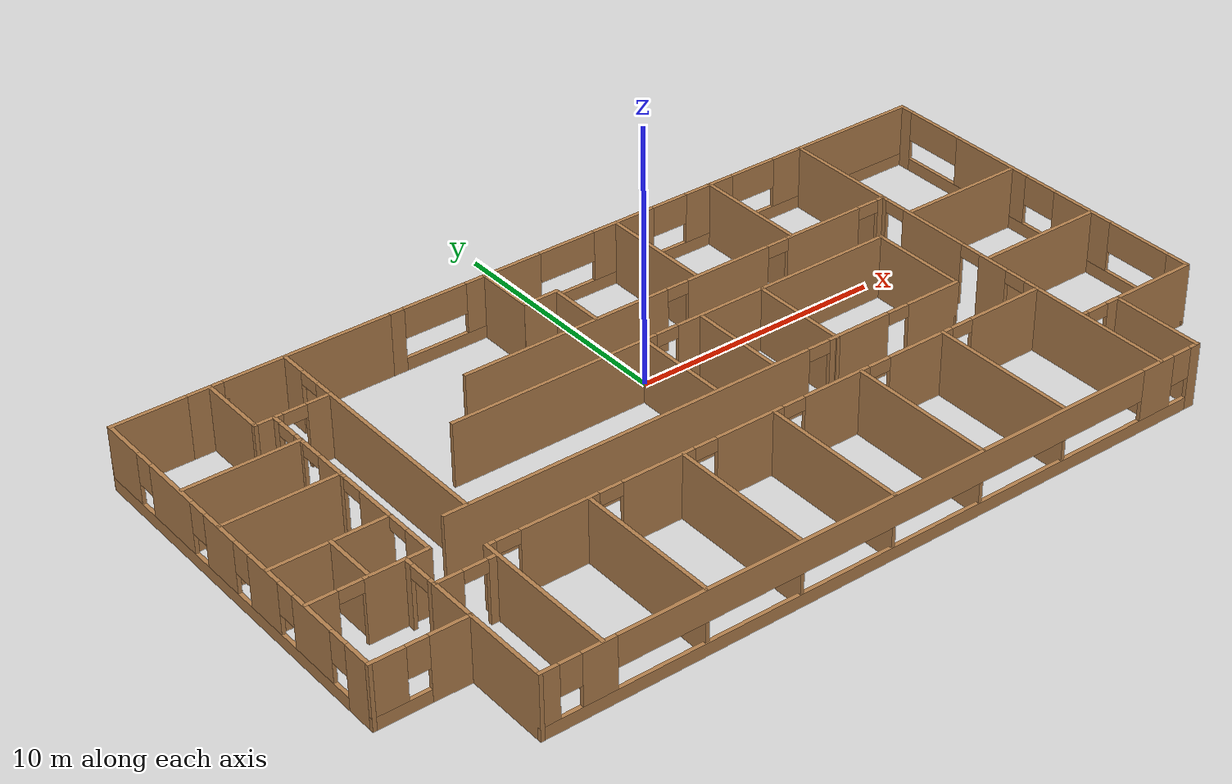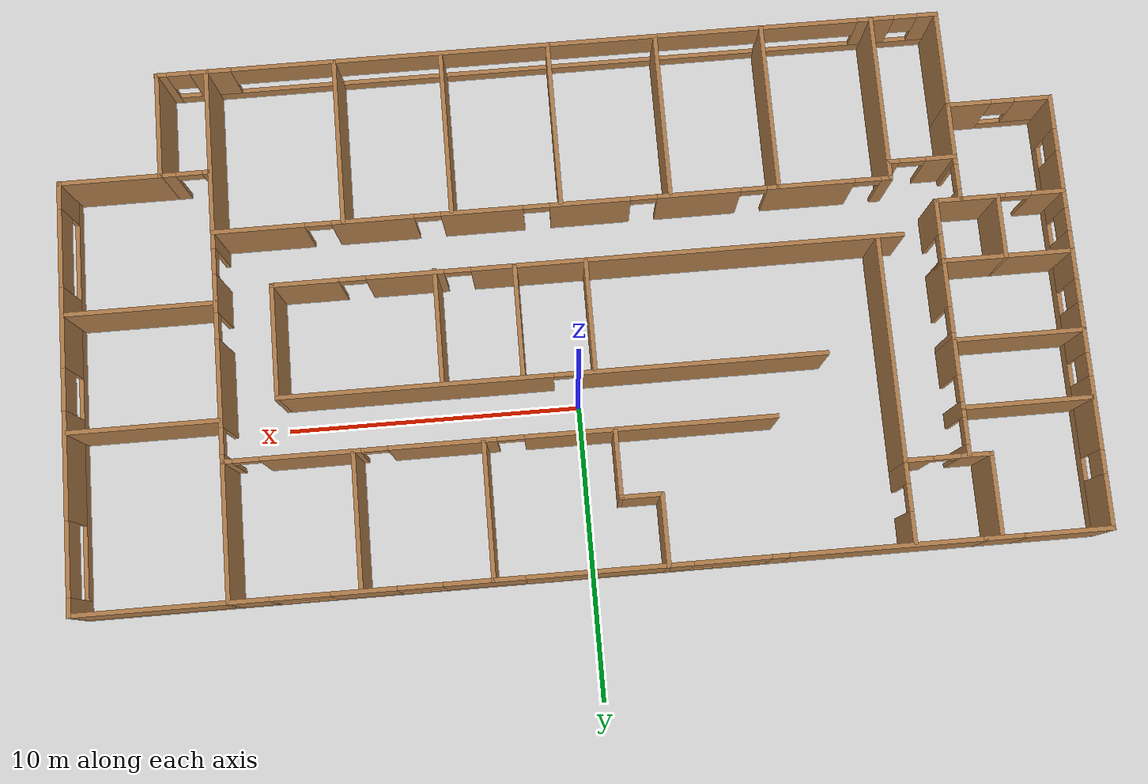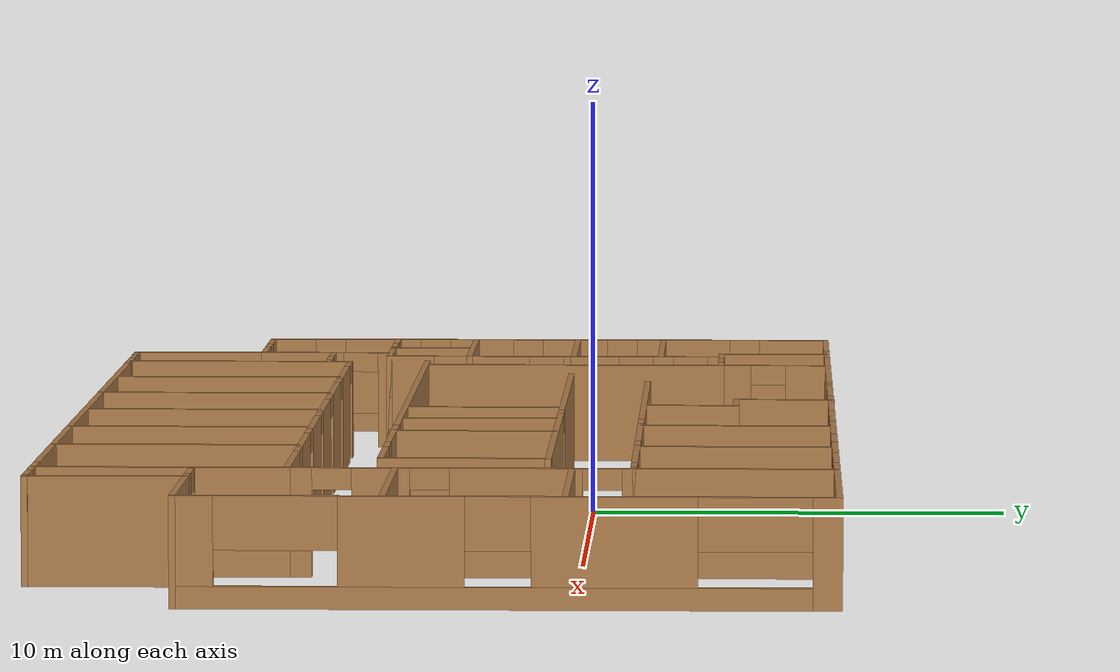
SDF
<?xml version='1.0'?>
<sdf version='1.5'>
  <model name='Office'>
    <pose>0 0 0 0 0 0</pose>
    <link name='Wall_10'>
      <collision name='Wall_10_Collision'>
        <geometry>
          <box>
            <size>3 0.15 2.5</size>
          </box>
        </geometry>
        <pose>0 0 1.25 0 -0 0</pose>
      </collision>
      <visual name='Wall_10_Visual'>
        <pose>0 0 1.25 0 -0 0</pose>
        <geometry>
          <box>
            <size>3 0.15 2.5</size>
          </box>
        </geometry>
        <material>
          <script>
            <uri>file://media/materials/scripts/gazebo.material</uri>
            <name>Gazebo/Wood</name>
          </script>
          <ambient>1 1 1 1</ambient>
        </material>
      </visual>
      <pose>-15.5998 5.80875 0 0 -0 0</pose>
    </link>
    <link name='Wall_14'>
      <collision name='Wall_14_Collision'>
        <geometry>
          <box>
            <size>1.5 0.15 2.5</size>
          </box>
        </geometry>
        <pose>0 0 1.25 0 -0 0</pose>
      </collision>
      <visual name='Wall_14_Visual'>
        <pose>0 0 1.25 0 -0 0</pose>
        <geometry>
          <box>
            <size>1.5 0.15 2.5</size>
          </box>
        </geometry>
        <material>
          <script>
            <uri>file://media/materials/scripts/gazebo.material</uri>
            <name>Gazebo/Wood</name>
          </script>
          <ambient>1 1 1 1</ambient>
        </material>
      </visual>
      <pose>-13.4998 5.80875 0 0 -0 0</pose>
    </link>
    <link name='Wall_15'>
      <collision name='Wall_15_Collision'>
        <geometry>
          <box>
            <size>6.5 0.15 2.5</size>
          </box>
        </geometry>
        <pose>0 0 1.25 0 -0 0</pose>
      </collision>
      <visual name='Wall_15_Visual'>
        <pose>0 0 1.25 0 -0 0</pose>
        <geometry>
          <box>
            <size>6.5 0.15 2.5</size>
          </box>
        </geometry>
        <material>
          <script>
            <uri>file://media/materials/scripts/gazebo.material</uri>
            <name>Gazebo/Wood</name>
          </script>
          <ambient>1 1 1 1</ambient>
        </material>
      </visual>
      <pose>-9.64979 5.80875 0 0 -0 0</pose>
    </link>
    <link name='Wall_19'>
      <pose>2.70021 1.20875 0 0 -0 0</pose>
      <visual name='Wall_19_Visual_0'>
        <pose>-5.01824 0 1.25 0 -0 0</pose>
        <geometry>
          <box>
            <size>8.46352 0.15 2.5</size>
          </box>
        </geometry>
        <material>
          <script>
            <uri>file://media/materials/scripts/gazebo.material</uri>
            <name>Gazebo/Wood</name>
          </script>
          <ambient>1 1 1 1</ambient>
        </material>
      </visual>
      <collision name='Wall_19_Collision_0'>
        <geometry>
          <box>
            <size>8.46352 0.15 2.5</size>
          </box>
        </geometry>
        <pose>-5.01824 0 1.25 0 -0 0</pose>
      </collision>
      <visual name='Wall_19_Visual_1'>
        <pose>1.91202 0 1.25 0 -0 0</pose>
        <geometry>
          <box>
            <size>3.59698 0.15 2.5</size>
          </box>
        </geometry>
        <material>
          <script>
            <uri>file://media/materials/scripts/gazebo.material</uri>
            <name>Gazebo/Wood</name>
          </script>
          <ambient>1 1 1 1</ambient>
        </material>
      </visual>
      <collision name='Wall_19_Collision_1'>
        <geometry>
          <box>
            <size>3.59698 0.15 2.5</size>
          </box>
        </geometry>
        <pose>1.91202 0 1.25 0 -0 0</pose>
      </collision>
      <visual name='Wall_19_Visual_2'>
        <pose>6.28533 0 1.25 0 -0 0</pose>
        <geometry>
          <box>
            <size>3.34965 0.15 2.5</size>
          </box>
        </geometry>
        <material>
          <script>
            <uri>file://media/materials/scripts/gazebo.material</uri>
            <name>Gazebo/Wood</name>
          </script>
          <ambient>1 1 1 1</ambient>
        </material>
      </visual>
      <collision name='Wall_19_Collision_2'>
        <geometry>
          <box>
            <size>3.34965 0.15 2.5</size>
          </box>
        </geometry>
        <pose>6.28533 0 1.25 0 -0 0</pose>
      </collision>
      <visual name='Wall_19_Visual_3'>
        <pose>9.05508 0 1.25 0 -0 0</pose>
        <geometry>
          <box>
            <size>0.389848 0.15 2.5</size>
          </box>
        </geometry>
        <material>
          <script>
            <uri>file://media/materials/scripts/gazebo.material</uri>
            <name>Gazebo/Wood</name>
          </script>
          <ambient>1 1 1 1</ambient>
        </material>
      </visual>
      <collision name='Wall_19_Collision_3'>
        <geometry>
          <box>
            <size>0.389848 0.15 2.5</size>
          </box>
        </geometry>
        <pose>9.05508 0 1.25 0 -0 0</pose>
      </collision>
      <visual name='Wall_19_Visual_4'>
        <pose>-0.336476 0 2.25 0 -0 0</pose>
        <geometry>
          <box>
            <size>0.9 0.15 0.5</size>
          </box>
        </geometry>
        <material>
          <script>
            <uri>file://media/materials/scripts/gazebo.material</uri>
            <name>Gazebo/Wood</name>
          </script>
          <ambient>1 1 1 1</ambient>
        </material>
      </visual>
      <collision name='Wall_19_Collision_4'>
        <geometry>
          <box>
            <size>0.9 0.15 0.5</size>
          </box>
        </geometry>
        <pose>-0.336476 0 2.25 0 -0 0</pose>
      </collision>
      <visual name='Wall_19_Visual_5'>
        <pose>4.1605 0 2.25 0 -0 0</pose>
        <geometry>
          <box>
            <size>0.9 0.15 0.5</size>
          </box>
        </geometry>
        <material>
          <script>
            <uri>file://media/materials/scripts/gazebo.material</uri>
            <name>Gazebo/Wood</name>
          </script>
          <ambient>1 1 1 1</ambient>
        </material>
      </visual>
      <collision name='Wall_19_Collision_5'>
        <geometry>
          <box>
            <size>0.9 0.15 0.5</size>
          </box>
        </geometry>
        <pose>4.1605 0 2.25 0 -0 0</pose>
      </collision>
      <visual name='Wall_19_Visual_6'>
        <pose>8.41015 0 2.25 0 -0 0</pose>
        <geometry>
          <box>
            <size>0.9 0.15 0.5</size>
          </box>
        </geometry>
        <material>
          <script>
            <uri>file://media/materials/scripts/gazebo.material</uri>
            <name>Gazebo/Wood</name>
          </script>
          <ambient>1 1 1 1</ambient>
        </material>
      </visual>
      <collision name='Wall_19_Collision_6'>
        <geometry>
          <box>
            <size>0.9 0.15 0.5</size>
          </box>
        </geometry>
        <pose>8.41015 0 2.25 0 -0 0</pose>
      </collision>
    </link>
    <link name='Wall_2'>
      <pose>5.35021 5.80875 0 0 -0 0</pose>
      <visual name='Wall_2_Visual_0'>
        <pose>-11.4699 0 1.25 0 -0 0</pose>
        <geometry>
          <box>
            <size>0.560252 0.15 2.5</size>
          </box>
        </geometry>
        <material>
          <script>
            <uri>file://media/materials/scripts/gazebo.material</uri>
            <name>Gazebo/Wood</name>
          </script>
          <ambient>1 1 1 1</ambient>
        </material>
      </visual>
      <collision name='Wall_2_Collision_0'>
        <geometry>
          <box>
            <size>0.560252 0.15 2.5</size>
          </box>
        </geometry>
        <pose>-11.4699 0 1.25 0 -0 0</pose>
      </collision>
      <visual name='Wall_2_Visual_1'>
        <pose>0.280126 0 0.25 0 -0 0</pose>
        <geometry>
          <box>
            <size>22.9397 0.15 0.5</size>
          </box>
        </geometry>
        <material>
          <script>
            <uri>file://media/materials/scripts/gazebo.material</uri>
            <name>Gazebo/Wood</name>
          </script>
          <ambient>1 1 1 1</ambient>
        </material>
      </visual>
      <collision name='Wall_2_Collision_1'>
        <geometry>
          <box>
            <size>22.9397 0.15 0.5</size>
          </box>
        </geometry>
        <pose>0.280126 0 0.25 0 -0 0</pose>
      </collision>
      <visual name='Wall_2_Visual_2'>
        <pose>-7.05725 0 1.5 0 -0 0</pose>
        <geometry>
          <box>
            <size>3.15734 0.15 2</size>
          </box>
        </geometry>
        <material>
          <script>
            <uri>file://media/materials/scripts/gazebo.material</uri>
            <name>Gazebo/Wood</name>
          </script>
          <ambient>1 1 1 1</ambient>
        </material>
      </visual>
      <collision name='Wall_2_Collision_2'>
        <geometry>
          <box>
            <size>3.15734 0.15 2</size>
          </box>
        </geometry>
        <pose>-7.05725 0 1.5 0 -0 0</pose>
      </collision>
      <visual name='Wall_2_Visual_3'>
        <pose>-1.78454 0 1.5 0 -0 0</pose>
        <geometry>
          <box>
            <size>2.68516 0.15 2</size>
          </box>
        </geometry>
        <material>
          <script>
            <uri>file://media/materials/scripts/gazebo.material</uri>
            <name>Gazebo/Wood</name>
          </script>
          <ambient>1 1 1 1</ambient>
        </material>
      </visual>
      <collision name='Wall_2_Collision_3'>
        <geometry>
          <box>
            <size>2.68516 0.15 2</size>
          </box>
        </geometry>
        <pose>-1.78454 0 1.5 0 -0 0</pose>
      </collision>
      <visual name='Wall_2_Visual_4'>
        <pose>2.13907 0 1.5 0 -0 0</pose>
        <geometry>
          <box>
            <size>2.16801 0.15 2</size>
          </box>
        </geometry>
        <material>
          <script>
            <uri>file://media/materials/scripts/gazebo.material</uri>
            <name>Gazebo/Wood</name>
          </script>
          <ambient>1 1 1 1</ambient>
        </material>
      </visual>
      <collision name='Wall_2_Collision_4'>
        <geometry>
          <box>
            <size>2.16801 0.15 2</size>
          </box>
        </geometry>
        <pose>2.13907 0 1.5 0 -0 0</pose>
      </collision>
      <visual name='Wall_2_Visual_5'>
        <pose>8.47114 0 1.5 0 -0 0</pose>
        <geometry>
          <box>
            <size>6.55771 0.15 2</size>
          </box>
        </geometry>
        <material>
          <script>
            <uri>file://media/materials/scripts/gazebo.material</uri>
            <name>Gazebo/Wood</name>
          </script>
          <ambient>1 1 1 1</ambient>
        </material>
      </visual>
      <collision name='Wall_2_Collision_5'>
        <geometry>
          <box>
            <size>6.55771 0.15 2</size>
          </box>
        </geometry>
        <pose>8.47114 0 1.5 0 -0 0</pose>
      </collision>
      <visual name='Wall_2_Visual_6'>
        <pose>-9.91284 0 1.9 0 -0 0</pose>
        <geometry>
          <box>
            <size>2.55382 0.15 1.2</size>
          </box>
        </geometry>
        <material>
          <script>
            <uri>file://media/materials/scripts/gazebo.material</uri>
            <name>Gazebo/Wood</name>
          </script>
          <ambient>1 1 1 1</ambient>
        </material>
      </visual>
      <collision name='Wall_2_Collision_6'>
        <geometry>
          <box>
            <size>2.55382 0.15 1.2</size>
          </box>
        </geometry>
        <pose>-9.91284 0 1.9 0 -0 0</pose>
      </collision>
      <visual name='Wall_2_Visual_7'>
        <pose>-4.30285 0 1.9 0 -0 0</pose>
        <geometry>
          <box>
            <size>2.35146 0.15 1.2</size>
          </box>
        </geometry>
        <material>
          <script>
            <uri>file://media/materials/scripts/gazebo.material</uri>
            <name>Gazebo/Wood</name>
          </script>
          <ambient>1 1 1 1</ambient>
        </material>
      </visual>
      <collision name='Wall_2_Collision_7'>
        <geometry>
          <box>
            <size>2.35146 0.15 1.2</size>
          </box>
        </geometry>
        <pose>-4.30285 0 1.9 0 -0 0</pose>
      </collision>
      <visual name='Wall_2_Visual_8'>
        <pose>0.306552 0 1.9 0 -0 0</pose>
        <geometry>
          <box>
            <size>1.49703 0.15 1.2</size>
          </box>
        </geometry>
        <material>
          <script>
            <uri>file://media/materials/scripts/gazebo.material</uri>
            <name>Gazebo/Wood</name>
          </script>
          <ambient>1 1 1 1</ambient>
        </material>
      </visual>
      <collision name='Wall_2_Collision_8'>
        <geometry>
          <box>
            <size>1.49703 0.15 1.2</size>
          </box>
        </geometry>
        <pose>0.306552 0 1.9 0 -0 0</pose>
      </collision>
      <visual name='Wall_2_Visual_9'>
        <pose>4.20768 0 1.9 0 -0 0</pose>
        <geometry>
          <box>
            <size>1.96921 0.15 1.2</size>
          </box>
        </geometry>
        <material>
          <script>
            <uri>file://media/materials/scripts/gazebo.material</uri>
            <name>Gazebo/Wood</name>
          </script>
          <ambient>1 1 1 1</ambient>
        </material>
      </visual>
      <collision name='Wall_2_Collision_9'>
        <geometry>
          <box>
            <size>1.96921 0.15 1.2</size>
          </box>
        </geometry>
        <pose>4.20768 0 1.9 0 -0 0</pose>
      </collision>
    </link>
    <link name='Wall_20'>
      <pose>11.8765 -2.716 0 0 0 -1.57047</pose>
      <visual name='Wall_20_Visual_0'>
        <pose>-3.83753 0 1.25 0 -0 0</pose>
        <geometry>
          <box>
            <size>0.324938 0.15 2.5</size>
          </box>
        </geometry>
        <material>
          <script>
            <uri>file://media/materials/scripts/gazebo.material</uri>
            <name>Gazebo/Wood</name>
          </script>
          <ambient>1 1 1 1</ambient>
        </material>
      </visual>
      <collision name='Wall_20_Collision_0'>
        <geometry>
          <box>
            <size>0.324938 0.15 2.5</size>
          </box>
        </geometry>
        <pose>-3.83753 0 1.25 0 -0 0</pose>
      </collision>
      <visual name='Wall_20_Visual_1'>
        <pose>-1.26988 0 1.25 0 -0 0</pose>
        <geometry>
          <box>
            <size>3.01037 0.15 2.5</size>
          </box>
        </geometry>
        <material>
          <script>
            <uri>file://media/materials/scripts/gazebo.material</uri>
            <name>Gazebo/Wood</name>
          </script>
          <ambient>1 1 1 1</ambient>
        </material>
      </visual>
      <collision name='Wall_20_Collision_1'>
        <geometry>
          <box>
            <size>3.01037 0.15 2.5</size>
          </box>
        </geometry>
        <pose>-1.26988 0 1.25 0 -0 0</pose>
      </collision>
      <visual name='Wall_20_Visual_2'>
        <pose>1.79718 0 1.25 0 -0 0</pose>
        <geometry>
          <box>
            <size>1.32373 0.15 2.5</size>
          </box>
        </geometry>
        <material>
          <script>
            <uri>file://media/materials/scripts/gazebo.material</uri>
            <name>Gazebo/Wood</name>
          </script>
          <ambient>1 1 1 1</ambient>
        </material>
      </visual>
      <collision name='Wall_20_Collision_2'>
        <geometry>
          <box>
            <size>1.32373 0.15 2.5</size>
          </box>
        </geometry>
        <pose>1.79718 0 1.25 0 -0 0</pose>
      </collision>
      <visual name='Wall_20_Visual_3'>
        <pose>3.67952 0 1.25 0 -0 0</pose>
        <geometry>
          <box>
            <size>0.640957 0.15 2.5</size>
          </box>
        </geometry>
        <material>
          <script>
            <uri>file://media/materials/scripts/gazebo.material</uri>
            <name>Gazebo/Wood</name>
          </script>
          <ambient>1 1 1 1</ambient>
        </material>
      </visual>
      <collision name='Wall_20_Collision_3'>
        <geometry>
          <box>
            <size>0.640957 0.15 2.5</size>
          </box>
        </geometry>
        <pose>3.67952 0 1.25 0 -0 0</pose>
      </collision>
      <visual name='Wall_20_Visual_4'>
        <pose>-3.22506 0 2.25 0 -0 0</pose>
        <geometry>
          <box>
            <size>0.9 0.15 0.5</size>
          </box>
        </geometry>
        <material>
          <script>
            <uri>file://media/materials/scripts/gazebo.material</uri>
            <name>Gazebo/Wood</name>
          </script>
          <ambient>1 1 1 1</ambient>
        </material>
      </visual>
      <collision name='Wall_20_Collision_4'>
        <geometry>
          <box>
            <size>0.9 0.15 0.5</size>
          </box>
        </geometry>
        <pose>-3.22506 0 2.25 0 -0 0</pose>
      </collision>
      <visual name='Wall_20_Visual_5'>
        <pose>0.685311 0 2.25 0 -0 0</pose>
        <geometry>
          <box>
            <size>0.9 0.15 0.5</size>
          </box>
        </geometry>
        <material>
          <script>
            <uri>file://media/materials/scripts/gazebo.material</uri>
            <name>Gazebo/Wood</name>
          </script>
          <ambient>1 1 1 1</ambient>
        </material>
      </visual>
      <collision name='Wall_20_Collision_5'>
        <geometry>
          <box>
            <size>0.9 0.15 0.5</size>
          </box>
        </geometry>
        <pose>0.685311 0 2.25 0 -0 0</pose>
      </collision>
      <visual name='Wall_20_Visual_6'>
        <pose>2.90904 0 2.25 0 -0 0</pose>
        <geometry>
          <box>
            <size>0.9 0.15 0.5</size>
          </box>
        </geometry>
        <material>
          <script>
            <uri>file://media/materials/scripts/gazebo.material</uri>
            <name>Gazebo/Wood</name>
          </script>
          <ambient>1 1 1 1</ambient>
        </material>
      </visual>
      <collision name='Wall_20_Collision_6'>
        <geometry>
          <box>
            <size>0.9 0.15 0.5</size>
          </box>
        </geometry>
        <pose>2.90904 0 2.25 0 -0 0</pose>
      </collision>
    </link>
    <link name='Wall_21'>
      <pose>0.327792 -6.64075 0 0 -0 3.14159</pose>
      <visual name='Wall_21_Visual_0'>
        <pose>-10.0278 0 1.25 0 -0 0</pose>
        <geometry>
          <box>
            <size>3.19439 0.15 2.5</size>
          </box>
        </geometry>
        <material>
          <script>
            <uri>file://media/materials/scripts/gazebo.material</uri>
            <name>Gazebo/Wood</name>
          </script>
          <ambient>1 1 1 1</ambient>
        </material>
      </visual>
      <collision name='Wall_21_Collision_0'>
        <geometry>
          <box>
            <size>3.19439 0.15 2.5</size>
          </box>
        </geometry>
        <pose>-10.0278 0 1.25 0 -0 0</pose>
      </collision>
      <visual name='Wall_21_Visual_1'>
        <pose>-6.12294 0 1.25 0 -0 0</pose>
        <geometry>
          <box>
            <size>2.81533 0.15 2.5</size>
          </box>
        </geometry>
        <material>
          <script>
            <uri>file://media/materials/scripts/gazebo.material</uri>
            <name>Gazebo/Wood</name>
          </script>
          <ambient>1 1 1 1</ambient>
        </material>
      </visual>
      <collision name='Wall_21_Collision_1'>
        <geometry>
          <box>
            <size>2.81533 0.15 2.5</size>
          </box>
        </geometry>
        <pose>-6.12294 0 1.25 0 -0 0</pose>
      </collision>
      <visual name='Wall_21_Visual_2'>
        <pose>-2.41333 0 1.25 0 -0 0</pose>
        <geometry>
          <box>
            <size>2.80389 0.15 2.5</size>
          </box>
        </geometry>
        <material>
          <script>
            <uri>file://media/materials/scripts/gazebo.material</uri>
            <name>Gazebo/Wood</name>
          </script>
          <ambient>1 1 1 1</ambient>
        </material>
      </visual>
      <collision name='Wall_21_Collision_2'>
        <geometry>
          <box>
            <size>2.80389 0.15 2.5</size>
          </box>
        </geometry>
        <pose>-2.41333 0 1.25 0 -0 0</pose>
      </collision>
      <visual name='Wall_21_Visual_3'>
        <pose>1.27186 0 1.25 0 -0 0</pose>
        <geometry>
          <box>
            <size>2.76648 0.15 2.5</size>
          </box>
        </geometry>
        <material>
          <script>
            <uri>file://media/materials/scripts/gazebo.material</uri>
            <name>Gazebo/Wood</name>
          </script>
          <ambient>1 1 1 1</ambient>
        </material>
      </visual>
      <collision name='Wall_21_Collision_3'>
        <geometry>
          <box>
            <size>2.76648 0.15 2.5</size>
          </box>
        </geometry>
        <pose>1.27186 0 1.25 0 -0 0</pose>
      </collision>
      <visual name='Wall_21_Visual_4'>
        <pose>4.99008 0 1.25 0 -0 0</pose>
        <geometry>
          <box>
            <size>2.86997 0.15 2.5</size>
          </box>
        </geometry>
        <material>
          <script>
            <uri>file://media/materials/scripts/gazebo.material</uri>
            <name>Gazebo/Wood</name>
          </script>
          <ambient>1 1 1 1</ambient>
        </material>
      </visual>
      <collision name='Wall_21_Collision_4'>
        <geometry>
          <box>
            <size>2.86997 0.15 2.5</size>
          </box>
        </geometry>
        <pose>4.99008 0 1.25 0 -0 0</pose>
      </collision>
      <visual name='Wall_21_Visual_5'>
        <pose>8.82658 0 1.25 0 -0 0</pose>
        <geometry>
          <box>
            <size>3.00303 0.15 2.5</size>
          </box>
        </geometry>
        <material>
          <script>
            <uri>file://media/materials/scripts/gazebo.material</uri>
            <name>Gazebo/Wood</name>
          </script>
          <ambient>1 1 1 1</ambient>
        </material>
      </visual>
      <collision name='Wall_21_Collision_5'>
        <geometry>
          <box>
            <size>3.00303 0.15 2.5</size>
          </box>
        </geometry>
        <pose>8.82658 0 1.25 0 -0 0</pose>
      </collision>
      <visual name='Wall_21_Visual_6'>
        <pose>11.4265 0 1.25 0 -0 0</pose>
        <geometry>
          <box>
            <size>0.396909 0.15 2.5</size>
          </box>
        </geometry>
        <material>
          <script>
            <uri>file://media/materials/scripts/gazebo.material</uri>
            <name>Gazebo/Wood</name>
          </script>
          <ambient>1 1 1 1</ambient>
        </material>
      </visual>
      <collision name='Wall_21_Collision_6'>
        <geometry>
          <box>
            <size>0.396909 0.15 2.5</size>
          </box>
        </geometry>
        <pose>11.4265 0 1.25 0 -0 0</pose>
      </collision>
      <visual name='Wall_21_Visual_7'>
        <pose>-7.98061 0 2.25 0 -0 0</pose>
        <geometry>
          <box>
            <size>0.9 0.15 0.5</size>
          </box>
        </geometry>
        <material>
          <script>
            <uri>file://media/materials/scripts/gazebo.material</uri>
            <name>Gazebo/Wood</name>
          </script>
          <ambient>1 1 1 1</ambient>
        </material>
      </visual>
      <collision name='Wall_21_Collision_7'>
        <geometry>
          <box>
            <size>0.9 0.15 0.5</size>
          </box>
        </geometry>
        <pose>-7.98061 0 2.25 0 -0 0</pose>
      </collision>
      <visual name='Wall_21_Visual_8'>
        <pose>-4.26528 0 2.25 0 -0 0</pose>
        <geometry>
          <box>
            <size>0.9 0.15 0.5</size>
          </box>
        </geometry>
        <material>
          <script>
            <uri>file://media/materials/scripts/gazebo.material</uri>
            <name>Gazebo/Wood</name>
          </script>
          <ambient>1 1 1 1</ambient>
        </material>
      </visual>
      <collision name='Wall_21_Collision_8'>
        <geometry>
          <box>
            <size>0.9 0.15 0.5</size>
          </box>
        </geometry>
        <pose>-4.26528 0 2.25 0 -0 0</pose>
      </collision>
      <visual name='Wall_21_Visual_9'>
        <pose>-0.561382 0 2.25 0 -0 0</pose>
        <geometry>
          <box>
            <size>0.9 0.15 0.5</size>
          </box>
        </geometry>
        <material>
          <script>
            <uri>file://media/materials/scripts/gazebo.material</uri>
            <name>Gazebo/Wood</name>
          </script>
          <ambient>1 1 1 1</ambient>
        </material>
      </visual>
      <collision name='Wall_21_Collision_9'>
        <geometry>
          <box>
            <size>0.9 0.15 0.5</size>
          </box>
        </geometry>
        <pose>-0.561382 0 2.25 0 -0 0</pose>
      </collision>
      <visual name='Wall_21_Visual_10'>
        <pose>3.1051 0 2.25 0 -0 0</pose>
        <geometry>
          <box>
            <size>0.9 0.15 0.5</size>
          </box>
        </geometry>
        <material>
          <script>
            <uri>file://media/materials/scripts/gazebo.material</uri>
            <name>Gazebo/Wood</name>
          </script>
          <ambient>1 1 1 1</ambient>
        </material>
      </visual>
      <collision name='Wall_21_Collision_10'>
        <geometry>
          <box>
            <size>0.9 0.15 0.5</size>
          </box>
        </geometry>
        <pose>3.1051 0 2.25 0 -0 0</pose>
      </collision>
      <visual name='Wall_21_Visual_11'>
        <pose>6.87507 0 2.25 0 -0 0</pose>
        <geometry>
          <box>
            <size>0.9 0.15 0.5</size>
          </box>
        </geometry>
        <material>
          <script>
            <uri>file://media/materials/scripts/gazebo.material</uri>
            <name>Gazebo/Wood</name>
          </script>
          <ambient>1 1 1 1</ambient>
        </material>
      </visual>
      <collision name='Wall_21_Collision_11'>
        <geometry>
          <box>
            <size>0.9 0.15 0.5</size>
          </box>
        </geometry>
        <pose>6.87507 0 2.25 0 -0 0</pose>
      </collision>
      <visual name='Wall_21_Visual_12'>
        <pose>10.7781 0 2.25 0 -0 0</pose>
        <geometry>
          <box>
            <size>0.9 0.15 0.5</size>
          </box>
        </geometry>
        <material>
          <script>
            <uri>file://media/materials/scripts/gazebo.material</uri>
            <name>Gazebo/Wood</name>
          </script>
          <ambient>1 1 1 1</ambient>
        </material>
      </visual>
      <collision name='Wall_21_Collision_12'>
        <geometry>
          <box>
            <size>0.9 0.15 0.5</size>
          </box>
        </geometry>
        <pose>10.7781 0 2.25 0 -0 0</pose>
      </collision>
    </link>
    <link name='Wall_26'>
      <collision name='Wall_26_Collision'>
        <geometry>
          <box>
            <size>3.75 0.15 2.5</size>
          </box>
        </geometry>
        <pose>0 0 1.25 0 -0 0</pose>
      </collision>
      <visual name='Wall_26_Visual'>
        <pose>0 0 1.25 0 -0 0</pose>
        <geometry>
          <box>
            <size>3.75 0.15 2.5</size>
          </box>
        </geometry>
        <material>
          <script>
            <uri>file://media/materials/scripts/gazebo.material</uri>
            <name>Gazebo/Wood</name>
          </script>
          <ambient>1 1 1 1</ambient>
        </material>
      </visual>
      <pose>13.5782 -10.5913 0 0 0 -1.5708</pose>
    </link>
    <link name='Wall_28'>
      <collision name='Wall_28_Collision'>
        <geometry>
          <box>
            <size>2 0.15 2.5</size>
          </box>
        </geometry>
        <pose>0 0 1.25 0 -0 0</pose>
      </collision>
      <visual name='Wall_28_Visual'>
        <pose>0 0 1.25 0 -0 0</pose>
        <geometry>
          <box>
            <size>2 0.15 2.5</size>
          </box>
        </geometry>
        <material>
          <script>
            <uri>file://media/materials/scripts/gazebo.material</uri>
            <name>Gazebo/Wood</name>
          </script>
          <ambient>1 1 1 1</ambient>
        </material>
      </visual>
      <pose>-13.4952 -8.13375 0 0 -0 1.5708</pose>
    </link>
    <link name='Wall_29'>
      <pose>-12.3617 -7.20875 0 0 -0 0</pose>
      <visual name='Wall_29_Visual_0'>
        <pose>-0.669337 0 1.25 0 -0 0</pose>
        <geometry>
          <box>
            <size>1.07833 0.15 2.5</size>
          </box>
        </geometry>
        <material>
          <script>
            <uri>file://media/materials/scripts/gazebo.material</uri>
            <name>Gazebo/Wood</name>
          </script>
          <ambient>1 1 1 1</ambient>
        </material>
      </visual>
      <collision name='Wall_29_Collision_0'>
        <geometry>
          <box>
            <size>1.07833 0.15 2.5</size>
          </box>
        </geometry>
        <pose>-0.669337 0 1.25 0 -0 0</pose>
      </collision>
      <visual name='Wall_29_Visual_1'>
        <pose>0.989163 0 1.25 0 -0 0</pose>
        <geometry>
          <box>
            <size>0.438674 0.15 2.5</size>
          </box>
        </geometry>
        <material>
          <script>
            <uri>file://media/materials/scripts/gazebo.material</uri>
            <name>Gazebo/Wood</name>
          </script>
          <ambient>1 1 1 1</ambient>
        </material>
      </visual>
      <collision name='Wall_29_Collision_1'>
        <geometry>
          <box>
            <size>0.438674 0.15 2.5</size>
          </box>
        </geometry>
        <pose>0.989163 0 1.25 0 -0 0</pose>
      </collision>
      <visual name='Wall_29_Visual_2'>
        <pose>0.319826 0 2.25 0 -0 0</pose>
        <geometry>
          <box>
            <size>0.9 0.15 0.5</size>
          </box>
        </geometry>
        <material>
          <script>
            <uri>file://media/materials/scripts/gazebo.material</uri>
            <name>Gazebo/Wood</name>
          </script>
          <ambient>1 1 1 1</ambient>
        </material>
      </visual>
      <collision name='Wall_29_Collision_2'>
        <geometry>
          <box>
            <size>0.9 0.15 0.5</size>
          </box>
        </geometry>
        <pose>0.319826 0 2.25 0 -0 0</pose>
      </collision>
    </link>
    <link name='Wall_3'>
      <pose>17.0252 -1.49125 0 0 0 -1.5708</pose>
      <visual name='Wall_3_Visual_0'>
        <pose>-7.0458 0 1.25 0 -0 0</pose>
        <geometry>
          <box>
            <size>0.658408 0.15 2.5</size>
          </box>
        </geometry>
        <material>
          <script>
            <uri>file://media/materials/scripts/gazebo.material</uri>
            <name>Gazebo/Wood</name>
          </script>
          <ambient>1 1 1 1</ambient>
        </material>
      </visual>
      <collision name='Wall_3_Collision_0'>
        <geometry>
          <box>
            <size>0.658408 0.15 2.5</size>
          </box>
        </geometry>
        <pose>-7.0458 0 1.25 0 -0 0</pose>
      </collision>
      <visual name='Wall_3_Visual_1'>
        <pose>0.329204 0 0.25 0 -0 0</pose>
        <geometry>
          <box>
            <size>14.0916 0.15 0.5</size>
          </box>
        </geometry>
        <material>
          <script>
            <uri>file://media/materials/scripts/gazebo.material</uri>
            <name>Gazebo/Wood</name>
          </script>
          <ambient>1 1 1 1</ambient>
        </material>
      </visual>
      <collision name='Wall_3_Collision_1'>
        <geometry>
          <box>
            <size>14.0916 0.15 0.5</size>
          </box>
        </geometry>
        <pose>0.329204 0 0.25 0 -0 0</pose>
      </collision>
      <visual name='Wall_3_Visual_2'>
        <pose>-2.38173 0 1.5 0 -0 0</pose>
        <geometry>
          <box>
            <size>3.65201 0.15 2</size>
          </box>
        </geometry>
        <material>
          <script>
            <uri>file://media/materials/scripts/gazebo.material</uri>
            <name>Gazebo/Wood</name>
          </script>
          <ambient>1 1 1 1</ambient>
        </material>
      </visual>
      <collision name='Wall_3_Collision_2'>
        <geometry>
          <box>
            <size>3.65201 0.15 2</size>
          </box>
        </geometry>
        <pose>-2.38173 0 1.5 0 -0 0</pose>
      </collision>
      <visual name='Wall_3_Visual_3'>
        <pose>2.2833 0 1.5 0 -0 0</pose>
        <geometry>
          <box>
            <size>2.77394 0.15 2</size>
          </box>
        </geometry>
        <material>
          <script>
            <uri>file://media/materials/scripts/gazebo.material</uri>
            <name>Gazebo/Wood</name>
          </script>
          <ambient>1 1 1 1</ambient>
        </material>
      </visual>
      <collision name='Wall_3_Collision_3'>
        <geometry>
          <box>
            <size>2.77394 0.15 2</size>
          </box>
        </geometry>
        <pose>2.2833 0 1.5 0 -0 0</pose>
      </collision>
      <visual name='Wall_3_Visual_4'>
        <pose>6.89046 0 1.5 0 -0 0</pose>
        <geometry>
          <box>
            <size>0.969072 0.15 2</size>
          </box>
        </geometry>
        <material>
          <script>
            <uri>file://media/materials/scripts/gazebo.material</uri>
            <name>Gazebo/Wood</name>
          </script>
          <ambient>1 1 1 1</ambient>
        </material>
      </visual>
      <collision name='Wall_3_Collision_4'>
        <geometry>
          <box>
            <size>0.969072 0.15 2</size>
          </box>
        </geometry>
        <pose>6.89046 0 1.5 0 -0 0</pose>
      </collision>
      <visual name='Wall_3_Visual_5'>
        <pose>-5.46217 0 1.9 0 -0 0</pose>
        <geometry>
          <box>
            <size>2.50885 0.15 1.2</size>
          </box>
        </geometry>
        <material>
          <script>
            <uri>file://media/materials/scripts/gazebo.material</uri>
            <name>Gazebo/Wood</name>
          </script>
          <ambient>1 1 1 1</ambient>
        </material>
      </visual>
      <collision name='Wall_3_Collision_5'>
        <geometry>
          <box>
            <size>2.50885 0.15 1.2</size>
          </box>
        </geometry>
        <pose>-5.46217 0 1.9 0 -0 0</pose>
      </collision>
      <visual name='Wall_3_Visual_6'>
        <pose>0.170302 0 1.9 0 -0 0</pose>
        <geometry>
          <box>
            <size>1.45206 0.15 1.2</size>
          </box>
        </geometry>
        <material>
          <script>
            <uri>file://media/materials/scripts/gazebo.material</uri>
            <name>Gazebo/Wood</name>
          </script>
          <ambient>1 1 1 1</ambient>
        </material>
      </visual>
      <collision name='Wall_3_Collision_6'>
        <geometry>
          <box>
            <size>1.45206 0.15 1.2</size>
          </box>
        </geometry>
        <pose>0.170302 0 1.9 0 -0 0</pose>
      </collision>
      <visual name='Wall_3_Visual_7'>
        <pose>5.0381 0 1.9 0 -0 0</pose>
        <geometry>
          <box>
            <size>2.73566 0.15 1.2</size>
          </box>
        </geometry>
        <material>
          <script>
            <uri>file://media/materials/scripts/gazebo.material</uri>
            <name>Gazebo/Wood</name>
          </script>
          <ambient>1 1 1 1</ambient>
        </material>
      </visual>
      <collision name='Wall_3_Collision_7'>
        <geometry>
          <box>
            <size>2.73566 0.15 1.2</size>
          </box>
        </geometry>
        <pose>5.0381 0 1.9 0 -0 0</pose>
      </collision>
    </link>
    <link name='Wall_33'>
      <collision name='Wall_33_Collision'>
        <geometry>
          <box>
            <size>5.881 0.15 2.5</size>
          </box>
        </geometry>
        <pose>0 0 1.25 0 -0 0</pose>
      </collision>
      <visual name='Wall_33_Visual'>
        <pose>0 0 1.25 0 -0 0</pose>
        <geometry>
          <box>
            <size>5.881 0.15 2.5</size>
          </box>
        </geometry>
        <material>
          <script>
            <uri>file://media/materials/scripts/gazebo.material</uri>
            <name>Gazebo/Wood</name>
          </script>
          <ambient>1 1 1 1</ambient>
        </material>
      </visual>
      <pose>-11.2222 -9.50625 0 0 0 -1.5708</pose>
    </link>
    <link name='Wall_36'>
      <collision name='Wall_36_Collision'>
        <geometry>
          <box>
            <size>5.866 0.15 2.5</size>
          </box>
        </geometry>
        <pose>0 0 1.25 0 -0 0</pose>
      </collision>
      <visual name='Wall_36_Visual'>
        <pose>0 0 1.25 0 -0 0</pose>
        <geometry>
          <box>
            <size>5.866 0.15 2.5</size>
          </box>
        </geometry>
        <material>
          <script>
            <uri>file://media/materials/scripts/gazebo.material</uri>
            <name>Gazebo/Wood</name>
          </script>
          <ambient>1 1 1 1</ambient>
        </material>
      </visual>
      <pose>-7.38821 -9.51375 0 0 0 -1.5708</pose>
    </link>
    <link name='Wall_38'>
      <collision name='Wall_38_Collision'>
        <geometry>
          <box>
            <size>5.8 0.15 2.5</size>
          </box>
        </geometry>
        <pose>0 0 1.25 0 -0 0</pose>
      </collision>
      <visual name='Wall_38_Visual'>
        <pose>0 0 1.25 0 -0 0</pose>
        <geometry>
          <box>
            <size>5.8 0.15 2.5</size>
          </box>
        </geometry>
        <material>
          <script>
            <uri>file://media/materials/scripts/gazebo.material</uri>
            <name>Gazebo/Wood</name>
          </script>
          <ambient>1 1 1 1</ambient>
        </material>
      </visual>
      <pose>-3.68921 -9.54675 0 0 0 -1.5708</pose>
    </link>
    <link name='Wall_4'>
      <collision name='Wall_4_Collision'>
        <geometry>
          <box>
            <size>3.59696 0.15 2.5</size>
          </box>
        </geometry>
        <pose>0 0 1.25 0 -0 0</pose>
      </collision>
      <visual name='Wall_4_Visual'>
        <pose>0 0 1.25 0 -0 0</pose>
        <geometry>
          <box>
            <size>3.59696 0.15 2.5</size>
          </box>
        </geometry>
        <material>
          <script>
            <uri>file://media/materials/scripts/gazebo.material</uri>
            <name>Gazebo/Wood</name>
          </script>
          <ambient>1 1 1 1</ambient>
        </material>
      </visual>
      <pose>15.3017 -8.79125 0 0 -0 3.14159</pose>
    </link>
    <link name='Wall_40'>
      <collision name='Wall_40_Collision'>
        <geometry>
          <box>
            <size>5.8 0.15 2.5</size>
          </box>
        </geometry>
        <pose>0 0 1.25 0 -0 0</pose>
      </collision>
      <visual name='Wall_40_Visual'>
        <pose>0 0 1.25 0 -0 0</pose>
        <geometry>
          <box>
            <size>5.8 0.15 2.5</size>
          </box>
        </geometry>
        <material>
          <script>
            <uri>file://media/materials/scripts/gazebo.material</uri>
            <name>Gazebo/Wood</name>
          </script>
          <ambient>1 1 1 1</ambient>
        </material>
      </visual>
      <pose>0.046792 -9.54675 0 0 0 -1.5708</pose>
    </link>
    <link name='Wall_42'>
      <collision name='Wall_42_Collision'>
        <geometry>
          <box>
            <size>5.8 0.15 2.5</size>
          </box>
        </geometry>
        <pose>0 0 1.25 0 -0 0</pose>
      </collision>
      <visual name='Wall_42_Visual'>
        <pose>0 0 1.25 0 -0 0</pose>
        <geometry>
          <box>
            <size>5.8 0.15 2.5</size>
          </box>
        </geometry>
        <material>
          <script>
            <uri>file://media/materials/scripts/gazebo.material</uri>
            <name>Gazebo/Wood</name>
          </script>
          <ambient>1 1 1 1</ambient>
        </material>
      </visual>
      <pose>3.77279 -9.54675 0 0 0 -1.5708</pose>
    </link>
    <link name='Wall_44'>
      <collision name='Wall_44_Collision'>
        <geometry>
          <box>
            <size>5.855 0.15 2.5</size>
          </box>
        </geometry>
        <pose>0 0 1.25 0 -0 0</pose>
      </collision>
      <visual name='Wall_44_Visual'>
        <pose>0 0 1.25 0 -0 0</pose>
        <geometry>
          <box>
            <size>5.855 0.15 2.5</size>
          </box>
        </geometry>
        <material>
          <script>
            <uri>file://media/materials/scripts/gazebo.material</uri>
            <name>Gazebo/Wood</name>
          </script>
          <ambient>1 1 1 1</ambient>
        </material>
      </visual>
      <pose>7.45979 -9.51925 0 0 0 -1.5708</pose>
    </link>
    <link name='Wall_47'>
      <collision name='Wall_47_Collision'>
        <geometry>
          <box>
            <size>5.881 0.15 2.5</size>
          </box>
        </geometry>
        <pose>0 0 1.25 0 -0 0</pose>
      </collision>
      <visual name='Wall_47_Visual'>
        <pose>0 0 1.25 0 -0 0</pose>
        <geometry>
          <box>
            <size>5.881 0.15 2.5</size>
          </box>
        </geometry>
        <material>
          <script>
            <uri>file://media/materials/scripts/gazebo.material</uri>
            <name>Gazebo/Wood</name>
          </script>
          <ambient>1 1 1 1</ambient>
        </material>
      </visual>
      <pose>11.8778 -9.50625 0 0 0 -1.5708</pose>
    </link>
    <link name='Wall_49'>
      <pose>12.7782 -8.79125 0 0 -0 3.14159</pose>
      <visual name='Wall_49_Visual_0'>
        <pose>-0.566515 0 1.25 0 -0 0</pose>
        <geometry>
          <box>
            <size>0.61697 0.15 2.5</size>
          </box>
        </geometry>
        <material>
          <script>
            <uri>file://media/materials/scripts/gazebo.material</uri>
            <name>Gazebo/Wood</name>
          </script>
          <ambient>1 1 1 1</ambient>
        </material>
      </visual>
      <collision name='Wall_49_Collision_0'>
        <geometry>
          <box>
            <size>0.61697 0.15 2.5</size>
          </box>
        </geometry>
        <pose>-0.566515 0 1.25 0 -0 0</pose>
      </collision>
      <visual name='Wall_49_Visual_1'>
        <pose>0.758485 0 1.25 0 -0 0</pose>
        <geometry>
          <box>
            <size>0.23303 0.15 2.5</size>
          </box>
        </geometry>
        <material>
          <script>
            <uri>file://media/materials/scripts/gazebo.material</uri>
            <name>Gazebo/Wood</name>
          </script>
          <ambient>1 1 1 1</ambient>
        </material>
      </visual>
      <collision name='Wall_49_Collision_1'>
        <geometry>
          <box>
            <size>0.23303 0.15 2.5</size>
          </box>
        </geometry>
        <pose>0.758485 0 1.25 0 -0 0</pose>
      </collision>
      <visual name='Wall_49_Visual_2'>
        <pose>0.19197 0 2.25 0 -0 0</pose>
        <geometry>
          <box>
            <size>0.9 0.15 0.5</size>
          </box>
        </geometry>
        <material>
          <script>
            <uri>file://media/materials/scripts/gazebo.material</uri>
            <name>Gazebo/Wood</name>
          </script>
          <ambient>1 1 1 1</ambient>
        </material>
      </visual>
      <collision name='Wall_49_Collision_2'>
        <geometry>
          <box>
            <size>0.9 0.15 0.5</size>
          </box>
        </geometry>
        <pose>0.19197 0 2.25 0 -0 0</pose>
      </collision>
    </link>
    <link name='Wall_51'>
      <pose>-14.8308 -5.69671 0 0 -0 0</pose>
      <visual name='Wall_51_Visual_0'>
        <pose>-1.66535 0 1.25 0 -0 0</pose>
        <geometry>
          <box>
            <size>1.16929 0.15 2.5</size>
          </box>
        </geometry>
        <material>
          <script>
            <uri>file://media/materials/scripts/gazebo.material</uri>
            <name>Gazebo/Wood</name>
          </script>
          <ambient>1 1 1 1</ambient>
        </material>
      </visual>
      <collision name='Wall_51_Collision_0'>
        <geometry>
          <box>
            <size>1.16929 0.15 2.5</size>
          </box>
        </geometry>
        <pose>-1.66535 0 1.25 0 -0 0</pose>
      </collision>
      <visual name='Wall_51_Visual_1'>
        <pose>1.03465 0 1.25 0 -0 0</pose>
        <geometry>
          <box>
            <size>2.43071 0.15 2.5</size>
          </box>
        </geometry>
        <material>
          <script>
            <uri>file://media/materials/scripts/gazebo.material</uri>
            <name>Gazebo/Wood</name>
          </script>
          <ambient>1 1 1 1</ambient>
        </material>
      </visual>
      <collision name='Wall_51_Collision_1'>
        <geometry>
          <box>
            <size>2.43071 0.15 2.5</size>
          </box>
        </geometry>
        <pose>1.03465 0 1.25 0 -0 0</pose>
      </collision>
      <visual name='Wall_51_Visual_2'>
        <pose>-0.63071 0 2.25 0 -0 0</pose>
        <geometry>
          <box>
            <size>0.9 0.15 0.5</size>
          </box>
        </geometry>
        <material>
          <script>
            <uri>file://media/materials/scripts/gazebo.material</uri>
            <name>Gazebo/Wood</name>
          </script>
          <ambient>1 1 1 1</ambient>
        </material>
      </visual>
      <collision name='Wall_51_Collision_2'>
        <geometry>
          <box>
            <size>0.9 0.15 0.5</size>
          </box>
        </geometry>
        <pose>-0.63071 0 2.25 0 -0 0</pose>
      </collision>
    </link>
    <link name='Wall_52'>
      <pose>-12.6558 -3.27171 0 0 -0 1.5708</pose>
      <visual name='Wall_52_Visual_0'>
        <pose>-1.8744 0 1.25 0 -0 0</pose>
        <geometry>
          <box>
            <size>1.25119 0.15 2.5</size>
          </box>
        </geometry>
        <material>
          <script>
            <uri>file://media/materials/scripts/gazebo.material</uri>
            <name>Gazebo/Wood</name>
          </script>
          <ambient>1 1 1 1</ambient>
        </material>
      </visual>
      <collision name='Wall_52_Collision_0'>
        <geometry>
          <box>
            <size>1.25119 0.15 2.5</size>
          </box>
        </geometry>
        <pose>-1.8744 0 1.25 0 -0 0</pose>
      </collision>
      <visual name='Wall_52_Visual_1'>
        <pose>0.459327 0 1.25 0 -0 0</pose>
        <geometry>
          <box>
            <size>1.61627 0.15 2.5</size>
          </box>
        </geometry>
        <material>
          <script>
            <uri>file://media/materials/scripts/gazebo.material</uri>
            <name>Gazebo/Wood</name>
          </script>
          <ambient>1 1 1 1</ambient>
        </material>
      </visual>
      <collision name='Wall_52_Collision_1'>
        <geometry>
          <box>
            <size>1.61627 0.15 2.5</size>
          </box>
        </geometry>
        <pose>0.459327 0 1.25 0 -0 0</pose>
      </collision>
      <visual name='Wall_52_Visual_2'>
        <pose>2.33373 0 1.25 0 -0 0</pose>
        <geometry>
          <box>
            <size>0.332538 0.15 2.5</size>
          </box>
        </geometry>
        <material>
          <script>
            <uri>file://media/materials/scripts/gazebo.material</uri>
            <name>Gazebo/Wood</name>
          </script>
          <ambient>1 1 1 1</ambient>
        </material>
      </visual>
      <collision name='Wall_52_Collision_2'>
        <geometry>
          <box>
            <size>0.332538 0.15 2.5</size>
          </box>
        </geometry>
        <pose>2.33373 0 1.25 0 -0 0</pose>
      </collision>
      <visual name='Wall_52_Visual_3'>
        <pose>-0.798807 0 2.25 0 -0 0</pose>
        <geometry>
          <box>
            <size>0.9 0.15 0.5</size>
          </box>
        </geometry>
        <material>
          <script>
            <uri>file://media/materials/scripts/gazebo.material</uri>
            <name>Gazebo/Wood</name>
          </script>
          <ambient>1 1 1 1</ambient>
        </material>
      </visual>
      <collision name='Wall_52_Collision_3'>
        <geometry>
          <box>
            <size>0.9 0.15 0.5</size>
          </box>
        </geometry>
        <pose>-0.798807 0 2.25 0 -0 0</pose>
      </collision>
      <visual name='Wall_52_Visual_4'>
        <pose>1.71746 0 2.25 0 -0 0</pose>
        <geometry>
          <box>
            <size>0.9 0.15 0.5</size>
          </box>
        </geometry>
        <material>
          <script>
            <uri>file://media/materials/scripts/gazebo.material</uri>
            <name>Gazebo/Wood</name>
          </script>
          <ambient>1 1 1 1</ambient>
        </material>
      </visual>
      <collision name='Wall_52_Collision_4'>
        <geometry>
          <box>
            <size>0.9 0.15 0.5</size>
          </box>
        </geometry>
        <pose>1.71746 0 2.25 0 -0 0</pose>
      </collision>
    </link>
    <link name='Wall_53'>
      <collision name='Wall_53_Collision'>
        <geometry>
          <box>
            <size>4.5 0.15 2.5</size>
          </box>
        </geometry>
        <pose>0 0 1.25 0 -0 0</pose>
      </collision>
      <visual name='Wall_53_Visual'>
        <pose>0 0 1.25 0 -0 0</pose>
        <geometry>
          <box>
            <size>4.5 0.15 2.5</size>
          </box>
        </geometry>
        <material>
          <script>
            <uri>file://media/materials/scripts/gazebo.material</uri>
            <name>Gazebo/Wood</name>
          </script>
          <ambient>1 1 1 1</ambient>
        </material>
      </visual>
      <pose>-14.8308 -0.846709 0 0 -0 3.14159</pose>
    </link>
    <link name='Wall_57'>
      <collision name='Wall_57_Collision'>
        <geometry>
          <box>
            <size>4.5 0.15 2.5</size>
          </box>
        </geometry>
        <pose>0 0 1.25 0 -0 0</pose>
      </collision>
      <visual name='Wall_57_Visual'>
        <pose>0 0 1.25 0 -0 0</pose>
        <geometry>
          <box>
            <size>4.5 0.15 2.5</size>
          </box>
        </geometry>
        <material>
          <script>
            <uri>file://media/materials/scripts/gazebo.material</uri>
            <name>Gazebo/Wood</name>
          </script>
          <ambient>1 1 1 1</ambient>
        </material>
      </visual>
      <pose>-14.8308 -3.59035 0 0 -0 0</pose>
    </link>
    <link name='Wall_59'>
      <collision name='Wall_59_Collision'>
        <geometry>
          <box>
            <size>2.25 0.15 2.5</size>
          </box>
        </geometry>
        <pose>0 0 1.25 0 -0 0</pose>
      </collision>
      <visual name='Wall_59_Visual'>
        <pose>0 0 1.25 0 -0 0</pose>
        <geometry>
          <box>
            <size>2.25 0.15 2.5</size>
          </box>
        </geometry>
        <material>
          <script>
            <uri>file://media/materials/scripts/gazebo.material</uri>
            <name>Gazebo/Wood</name>
          </script>
          <ambient>1 1 1 1</ambient>
        </material>
      </visual>
      <pose>-14.7695 -4.64035 0 0 0 -1.5708</pose>
    </link>
    <link name='Wall_6'>
      <pose>0.054792 -12.4088 0 0 -0 3.14159</pose>
      <visual name='Wall_6_Visual_0'>
        <pose>-13.398 0 1.25 0 -0 0</pose>
        <geometry>
          <box>
            <size>0.453995 0.15 2.5</size>
          </box>
        </geometry>
        <material>
          <script>
            <uri>file://media/materials/scripts/gazebo.material</uri>
            <name>Gazebo/Wood</name>
          </script>
          <ambient>1 1 1 1</ambient>
        </material>
      </visual>
      <collision name='Wall_6_Collision_0'>
        <geometry>
          <box>
            <size>0.453995 0.15 2.5</size>
          </box>
        </geometry>
        <pose>-13.398 0 1.25 0 -0 0</pose>
      </collision>
      <visual name='Wall_6_Visual_1'>
        <pose>0.226997 0 0.25 0 -0 0</pose>
        <geometry>
          <box>
            <size>26.796 0.15 0.5</size>
          </box>
        </geometry>
        <material>
          <script>
            <uri>file://media/materials/scripts/gazebo.material</uri>
            <name>Gazebo/Wood</name>
          </script>
          <ambient>1 1 1 1</ambient>
        </material>
      </visual>
      <collision name='Wall_6_Collision_1'>
        <geometry>
          <box>
            <size>26.796 0.15 0.5</size>
          </box>
        </geometry>
        <pose>0.226997 0 0.25 0 -0 0</pose>
      </collision>
      <visual name='Wall_6_Visual_2'>
        <pose>-11.6639 0 1.5 0 -0 0</pose>
        <geometry>
          <box>
            <size>1.41428 0.15 2</size>
          </box>
        </geometry>
        <material>
          <script>
            <uri>file://media/materials/scripts/gazebo.material</uri>
            <name>Gazebo/Wood</name>
          </script>
          <ambient>1 1 1 1</ambient>
        </material>
      </visual>
      <collision name='Wall_6_Collision_2'>
        <geometry>
          <box>
            <size>1.41428 0.15 2</size>
          </box>
        </geometry>
        <pose>-11.6639 0 1.5 0 -0 0</pose>
      </collision>
      <visual name='Wall_6_Visual_3'>
        <pose>11.4432 0 1.5 0 -0 0</pose>
        <geometry>
          <box>
            <size>1.27929 0.15 2</size>
          </box>
        </geometry>
        <material>
          <script>
            <uri>file://media/materials/scripts/gazebo.material</uri>
            <name>Gazebo/Wood</name>
          </script>
          <ambient>1 1 1 1</ambient>
        </material>
      </visual>
      <collision name='Wall_6_Collision_3'>
        <geometry>
          <box>
            <size>1.27929 0.15 2</size>
          </box>
        </geometry>
        <pose>11.4432 0 1.5 0 -0 0</pose>
      </collision>
      <visual name='Wall_6_Visual_4'>
        <pose>13.2539 0 1.5 0 -0 0</pose>
        <geometry>
          <box>
            <size>0.742142 0.15 2</size>
          </box>
        </geometry>
        <material>
          <script>
            <uri>file://media/materials/scripts/gazebo.material</uri>
            <name>Gazebo/Wood</name>
          </script>
          <ambient>1 1 1 1</ambient>
        </material>
      </visual>
      <collision name='Wall_6_Collision_4'>
        <geometry>
          <box>
            <size>0.742142 0.15 2</size>
          </box>
        </geometry>
        <pose>13.2539 0 1.5 0 -0 0</pose>
      </collision>
      <visual name='Wall_6_Visual_5'>
        <pose>-12.771 0 1.9 0 -0 0</pose>
        <geometry>
          <box>
            <size>0.8 0.15 1.2</size>
          </box>
        </geometry>
        <material>
          <script>
            <uri>file://media/materials/scripts/gazebo.material</uri>
            <name>Gazebo/Wood</name>
          </script>
          <ambient>1 1 1 1</ambient>
        </material>
      </visual>
      <collision name='Wall_6_Collision_5'>
        <geometry>
          <box>
            <size>0.8 0.15 1.2</size>
          </box>
        </geometry>
        <pose>-12.771 0 1.9 0 -0 0</pose>
      </collision>
      <visual name='Wall_6_Visual_6'>
        <pose>-0.076576 0 1.9 0 -0 0</pose>
        <geometry>
          <box>
            <size>21.7603 0.15 1.2</size>
          </box>
        </geometry>
        <material>
          <script>
            <uri>file://media/materials/scripts/gazebo.material</uri>
            <name>Gazebo/Wood</name>
          </script>
          <ambient>1 1 1 1</ambient>
        </material>
      </visual>
      <collision name='Wall_6_Collision_6'>
        <geometry>
          <box>
            <size>21.7603 0.15 1.2</size>
          </box>
        </geometry>
        <pose>-0.076576 0 1.9 0 -0 0</pose>
      </collision>
      <visual name='Wall_6_Visual_7'>
        <pose>12.4829 0 1.9 0 -0 0</pose>
        <geometry>
          <box>
            <size>0.8 0.15 1.2</size>
          </box>
        </geometry>
        <material>
          <script>
            <uri>file://media/materials/scripts/gazebo.material</uri>
            <name>Gazebo/Wood</name>
          </script>
          <ambient>1 1 1 1</ambient>
        </material>
      </visual>
      <collision name='Wall_6_Collision_7'>
        <geometry>
          <box>
            <size>0.8 0.15 1.2</size>
          </box>
        </geometry>
        <pose>12.4829 0 1.9 0 -0 0</pose>
      </collision>
    </link>
    <link name='Wall_61'>
      <pose>-0.695039 -4.62762 0 0 -0 0</pose>
      <visual name='Wall_61_Visual_0'>
        <pose>-3.39393 0 1.25 0 -0 0</pose>
        <geometry>
          <box>
            <size>14.7121 0.15 2.5</size>
          </box>
        </geometry>
        <material>
          <script>
            <uri>file://media/materials/scripts/gazebo.material</uri>
            <name>Gazebo/Wood</name>
          </script>
          <ambient>1 1 1 1</ambient>
        </material>
      </visual>
      <collision name='Wall_61_Collision_0'>
        <geometry>
          <box>
            <size>14.7121 0.15 2.5</size>
          </box>
        </geometry>
        <pose>-3.39393 0 1.25 0 -0 0</pose>
      </collision>
      <visual name='Wall_61_Visual_1'>
        <pose>6.1834 0 1.25 0 -0 0</pose>
        <geometry>
          <box>
            <size>2.6425 0.15 2.5</size>
          </box>
        </geometry>
        <material>
          <script>
            <uri>file://media/materials/scripts/gazebo.material</uri>
            <name>Gazebo/Wood</name>
          </script>
          <ambient>1 1 1 1</ambient>
        </material>
      </visual>
      <collision name='Wall_61_Collision_1'>
        <geometry>
          <box>
            <size>2.6425 0.15 2.5</size>
          </box>
        </geometry>
        <pose>6.1834 0 1.25 0 -0 0</pose>
      </collision>
      <visual name='Wall_61_Visual_2'>
        <pose>9.57732 0 1.25 0 -0 0</pose>
        <geometry>
          <box>
            <size>2.34536 0.15 2.5</size>
          </box>
        </geometry>
        <material>
          <script>
            <uri>file://media/materials/scripts/gazebo.material</uri>
            <name>Gazebo/Wood</name>
          </script>
          <ambient>1 1 1 1</ambient>
        </material>
      </visual>
      <collision name='Wall_61_Collision_2'>
        <geometry>
          <box>
            <size>2.34536 0.15 2.5</size>
          </box>
        </geometry>
        <pose>9.57732 0 1.25 0 -0 0</pose>
      </collision>
      <visual name='Wall_61_Visual_3'>
        <pose>4.41215 0 2.25 0 -0 0</pose>
        <geometry>
          <box>
            <size>0.9 0.15 0.5</size>
          </box>
        </geometry>
        <material>
          <script>
            <uri>file://media/materials/scripts/gazebo.material</uri>
            <name>Gazebo/Wood</name>
          </script>
          <ambient>1 1 1 1</ambient>
        </material>
      </visual>
      <collision name='Wall_61_Collision_3'>
        <geometry>
          <box>
            <size>0.9 0.15 0.5</size>
          </box>
        </geometry>
        <pose>4.41215 0 2.25 0 -0 0</pose>
      </collision>
      <visual name='Wall_61_Visual_4'>
        <pose>7.95465 0 2.25 0 -0 0</pose>
        <geometry>
          <box>
            <size>0.9 0.15 0.5</size>
          </box>
        </geometry>
        <material>
          <script>
            <uri>file://media/materials/scripts/gazebo.material</uri>
            <name>Gazebo/Wood</name>
          </script>
          <ambient>1 1 1 1</ambient>
        </material>
      </visual>
      <collision name='Wall_61_Collision_4'>
        <geometry>
          <box>
            <size>0.9 0.15 0.5</size>
          </box>
        </geometry>
        <pose>7.95465 0 2.25 0 -0 0</pose>
      </collision>
    </link>
    <link name='Wall_62'>
      <collision name='Wall_62_Collision'>
        <geometry>
          <box>
            <size>4 0.15 2.5</size>
          </box>
        </geometry>
        <pose>0 0 1.25 0 -0 0</pose>
      </collision>
      <visual name='Wall_62_Visual'>
        <pose>0 0 1.25 0 -0 0</pose>
        <geometry>
          <box>
            <size>4 0.15 2.5</size>
          </box>
        </geometry>
        <material>
          <script>
            <uri>file://media/materials/scripts/gazebo.material</uri>
            <name>Gazebo/Wood</name>
          </script>
          <ambient>1 1 1 1</ambient>
        </material>
      </visual>
      <pose>9.97996 -2.70262 0 0 -0 1.5708</pose>
    </link>
    <link name='Wall_63'>
      <pose>0.804961 -0.777624 0 0 -0 3.14159</pose>
      <visual name='Wall_63_Visual_0'>
        <pose>-4.6124 0 1.25 0 -0 0</pose>
        <geometry>
          <box>
            <size>9.2752 0.15 2.5</size>
          </box>
        </geometry>
        <material>
          <script>
            <uri>file://media/materials/scripts/gazebo.material</uri>
            <name>Gazebo/Wood</name>
          </script>
          <ambient>1 1 1 1</ambient>
        </material>
      </visual>
      <collision name='Wall_63_Collision_0'>
        <geometry>
          <box>
            <size>9.2752 0.15 2.5</size>
          </box>
        </geometry>
        <pose>-4.6124 0 1.25 0 -0 0</pose>
      </collision>
      <visual name='Wall_63_Visual_1'>
        <pose>5.0876 0 1.25 0 -0 0</pose>
        <geometry>
          <box>
            <size>8.3248 0.15 2.5</size>
          </box>
        </geometry>
        <material>
          <script>
            <uri>file://media/materials/scripts/gazebo.material</uri>
            <name>Gazebo/Wood</name>
          </script>
          <ambient>1 1 1 1</ambient>
        </material>
      </visual>
      <collision name='Wall_63_Collision_1'>
        <geometry>
          <box>
            <size>8.3248 0.15 2.5</size>
          </box>
        </geometry>
        <pose>5.0876 0 1.25 0 -0 0</pose>
      </collision>
      <visual name='Wall_63_Visual_2'>
        <pose>0.475202 0 2.25 0 -0 0</pose>
        <geometry>
          <box>
            <size>0.9 0.15 0.5</size>
          </box>
        </geometry>
        <material>
          <script>
            <uri>file://media/materials/scripts/gazebo.material</uri>
            <name>Gazebo/Wood</name>
          </script>
          <ambient>1 1 1 1</ambient>
        </material>
      </visual>
      <collision name='Wall_63_Collision_2'>
        <geometry>
          <box>
            <size>0.9 0.15 0.5</size>
          </box>
        </geometry>
        <pose>0.475202 0 2.25 0 -0 0</pose>
      </collision>
    </link>
    <link name='Wall_65'>
      <collision name='Wall_65_Collision'>
        <geometry>
          <box>
            <size>3.83063 0.15 2.5</size>
          </box>
        </geometry>
        <pose>0 0 1.25 0 -0 0</pose>
      </collision>
      <visual name='Wall_65_Visual'>
        <pose>0 0 1.25 0 -0 0</pose>
        <geometry>
          <box>
            <size>3.83063 0.15 2.5</size>
          </box>
        </geometry>
        <material>
          <script>
            <uri>file://media/materials/scripts/gazebo.material</uri>
            <name>Gazebo/Wood</name>
          </script>
          <ambient>1 1 1 1</ambient>
        </material>
      </visual>
      <pose>-0.622208 -2.73225 0 0 0 -1.5708</pose>
    </link>
    <link name='Wall_67'>
      <collision name='Wall_67_Collision'>
        <geometry>
          <box>
            <size>3.86502 0.15 2.5</size>
          </box>
        </geometry>
        <pose>0 0 1.25 0 -0 0</pose>
      </collision>
      <visual name='Wall_67_Visual'>
        <pose>0 0 1.25 0 -0 0</pose>
        <geometry>
          <box>
            <size>3.86502 0.15 2.5</size>
          </box>
        </geometry>
        <material>
          <script>
            <uri>file://media/materials/scripts/gazebo.material</uri>
            <name>Gazebo/Wood</name>
          </script>
          <ambient>1 1 1 1</ambient>
        </material>
      </visual>
      <pose>1.78479 -2.74925 0 0 0 -1.5708</pose>
    </link>
    <link name='Wall_69'>
      <collision name='Wall_69_Collision'>
        <geometry>
          <box>
            <size>4 0.15 2.5</size>
          </box>
        </geometry>
        <pose>0 0 1.25 0 -0 0</pose>
      </collision>
      <visual name='Wall_69_Visual'>
        <pose>0 0 1.25 0 -0 0</pose>
        <geometry>
          <box>
            <size>4 0.15 2.5</size>
          </box>
        </geometry>
        <material>
          <script>
            <uri>file://media/materials/scripts/gazebo.material</uri>
            <name>Gazebo/Wood</name>
          </script>
          <ambient>1 1 1 1</ambient>
        </material>
      </visual>
      <pose>4.48434 -2.75055 0 0 0 -1.5708</pose>
    </link>
    <link name='Wall_7'>
      <collision name='Wall_7_Collision'>
        <geometry>
          <box>
            <size>3.5 0.15 2.5</size>
          </box>
        </geometry>
        <pose>0 0 1.25 0 -0 0</pose>
      </collision>
      <visual name='Wall_7_Visual'>
        <pose>0 0 1.25 0 -0 0</pose>
        <geometry>
          <box>
            <size>3.5 0.15 2.5</size>
          </box>
        </geometry>
        <material>
          <script>
            <uri>file://media/materials/scripts/gazebo.material</uri>
            <name>Gazebo/Wood</name>
          </script>
          <ambient>1 1 1 1</ambient>
        </material>
      </visual>
      <pose>-13.4952 -10.7338 0 0 -0 1.5708</pose>
    </link>
    <link name='Wall_71'>
      <pose>-12.6558 1.07829 0 0 -0 1.5708</pose>
      <visual name='Wall_71_Visual_0'>
        <pose>-1.36814 0 1.25 0 -0 0</pose>
        <geometry>
          <box>
            <size>1.26371 0.15 2.5</size>
          </box>
        </geometry>
        <material>
          <script>
            <uri>file://media/materials/scripts/gazebo.material</uri>
            <name>Gazebo/Wood</name>
          </script>
          <ambient>1 1 1 1</ambient>
        </material>
      </visual>
      <collision name='Wall_71_Collision_0'>
        <geometry>
          <box>
            <size>1.26371 0.15 2.5</size>
          </box>
        </geometry>
        <pose>-1.36814 0 1.25 0 -0 0</pose>
      </collision>
      <visual name='Wall_71_Visual_1'>
        <pose>0.427789 0 1.25 0 -0 0</pose>
        <geometry>
          <box>
            <size>0.528153 0.15 2.5</size>
          </box>
        </geometry>
        <material>
          <script>
            <uri>file://media/materials/scripts/gazebo.material</uri>
            <name>Gazebo/Wood</name>
          </script>
          <ambient>1 1 1 1</ambient>
        </material>
      </visual>
      <collision name='Wall_71_Collision_1'>
        <geometry>
          <box>
            <size>0.528153 0.15 2.5</size>
          </box>
        </geometry>
        <pose>0.427789 0 1.25 0 -0 0</pose>
      </collision>
      <visual name='Wall_71_Visual_2'>
        <pose>1.79593 0 1.25 0 -0 0</pose>
        <geometry>
          <box>
            <size>0.408135 0.15 2.5</size>
          </box>
        </geometry>
        <material>
          <script>
            <uri>file://media/materials/scripts/gazebo.material</uri>
            <name>Gazebo/Wood</name>
          </script>
          <ambient>1 1 1 1</ambient>
        </material>
      </visual>
      <collision name='Wall_71_Collision_2'>
        <geometry>
          <box>
            <size>0.408135 0.15 2.5</size>
          </box>
        </geometry>
        <pose>1.79593 0 1.25 0 -0 0</pose>
      </collision>
      <visual name='Wall_71_Visual_3'>
        <pose>-0.286287 0 2.25 0 -0 0</pose>
        <geometry>
          <box>
            <size>0.9 0.15 0.5</size>
          </box>
        </geometry>
        <material>
          <script>
            <uri>file://media/materials/scripts/gazebo.material</uri>
            <name>Gazebo/Wood</name>
          </script>
          <ambient>1 1 1 1</ambient>
        </material>
      </visual>
      <collision name='Wall_71_Collision_3'>
        <geometry>
          <box>
            <size>0.9 0.15 0.5</size>
          </box>
        </geometry>
        <pose>-0.286287 0 2.25 0 -0 0</pose>
      </collision>
      <visual name='Wall_71_Visual_4'>
        <pose>1.14186 0 2.25 0 -0 0</pose>
        <geometry>
          <box>
            <size>0.9 0.15 0.5</size>
          </box>
        </geometry>
        <material>
          <script>
            <uri>file://media/materials/scripts/gazebo.material</uri>
            <name>Gazebo/Wood</name>
          </script>
          <ambient>1 1 1 1</ambient>
        </material>
      </visual>
      <collision name='Wall_71_Collision_4'>
        <geometry>
          <box>
            <size>0.9 0.15 0.5</size>
          </box>
        </geometry>
        <pose>1.14186 0 2.25 0 -0 0</pose>
      </collision>
    </link>
    <link name='Wall_74'>
      <collision name='Wall_74_Collision'>
        <geometry>
          <box>
            <size>4.394 0.15 2.5</size>
          </box>
        </geometry>
        <pose>0 0 1.25 0 -0 0</pose>
      </collision>
      <visual name='Wall_74_Visual'>
        <pose>0 0 1.25 0 -0 0</pose>
        <geometry>
          <box>
            <size>4.394 0.15 2.5</size>
          </box>
        </geometry>
        <material>
          <script>
            <uri>file://media/materials/scripts/gazebo.material</uri>
            <name>Gazebo/Wood</name>
          </script>
          <ambient>1 1 1 1</ambient>
        </material>
      </visual>
      <pose>-14.8162 1.44825 0 0 -0 0</pose>
    </link>
    <link name='Wall_76'>
      <pose>-11.9562 3.03925 0 0 -0 0</pose>
      <visual name='Wall_76_Visual_0'>
        <pose>-0.950696 0 1.25 0 -0 0</pose>
        <geometry>
          <box>
            <size>1.09861 0.15 2.5</size>
          </box>
        </geometry>
        <material>
          <script>
            <uri>file://media/materials/scripts/gazebo.material</uri>
            <name>Gazebo/Wood</name>
          </script>
          <ambient>1 1 1 1</ambient>
        </material>
      </visual>
      <collision name='Wall_76_Collision_0'>
        <geometry>
          <box>
            <size>1.09861 0.15 2.5</size>
          </box>
        </geometry>
        <pose>-0.950696 0 1.25 0 -0 0</pose>
      </collision>
      <visual name='Wall_76_Visual_1'>
        <pose>0.999304 0 1.25 0 -0 0</pose>
        <geometry>
          <box>
            <size>1.00139 0.15 2.5</size>
          </box>
        </geometry>
        <material>
          <script>
            <uri>file://media/materials/scripts/gazebo.material</uri>
            <name>Gazebo/Wood</name>
          </script>
          <ambient>1 1 1 1</ambient>
        </material>
      </visual>
      <collision name='Wall_76_Collision_1'>
        <geometry>
          <box>
            <size>1.00139 0.15 2.5</size>
          </box>
        </geometry>
        <pose>0.999304 0 1.25 0 -0 0</pose>
      </collision>
      <visual name='Wall_76_Visual_2'>
        <pose>0.048609 0 2.25 0 -0 0</pose>
        <geometry>
          <box>
            <size>0.9 0.15 0.5</size>
          </box>
        </geometry>
        <material>
          <script>
            <uri>file://media/materials/scripts/gazebo.material</uri>
            <name>Gazebo/Wood</name>
          </script>
          <ambient>1 1 1 1</ambient>
        </material>
      </visual>
      <collision name='Wall_76_Collision_2'>
        <geometry>
          <box>
            <size>0.9 0.15 0.5</size>
          </box>
        </geometry>
        <pose>0.048609 0 2.25 0 -0 0</pose>
      </collision>
    </link>
    <link name='Wall_77'>
      <pose>-10.5312 4.38375 0 0 -0 1.5708</pose>
      <visual name='Wall_77_Visual_0'>
        <pose>-0.992696 0 1.25 0 -0 0</pose>
        <geometry>
          <box>
            <size>0.853609 0.15 2.5</size>
          </box>
        </geometry>
        <material>
          <script>
            <uri>file://media/materials/scripts/gazebo.material</uri>
            <name>Gazebo/Wood</name>
          </script>
          <ambient>1 1 1 1</ambient>
        </material>
      </visual>
      <collision name='Wall_77_Collision_0'>
        <geometry>
          <box>
            <size>0.853609 0.15 2.5</size>
          </box>
        </geometry>
        <pose>-0.992696 0 1.25 0 -0 0</pose>
      </collision>
      <visual name='Wall_77_Visual_1'>
        <pose>0.876804 0 1.25 0 -0 0</pose>
        <geometry>
          <box>
            <size>1.08539 0.15 2.5</size>
          </box>
        </geometry>
        <material>
          <script>
            <uri>file://media/materials/scripts/gazebo.material</uri>
            <name>Gazebo/Wood</name>
          </script>
          <ambient>1 1 1 1</ambient>
        </material>
      </visual>
      <collision name='Wall_77_Collision_1'>
        <geometry>
          <box>
            <size>1.08539 0.15 2.5</size>
          </box>
        </geometry>
        <pose>0.876804 0 1.25 0 -0 0</pose>
      </collision>
      <visual name='Wall_77_Visual_2'>
        <pose>-0.115891 0 2.25 0 -0 0</pose>
        <geometry>
          <box>
            <size>0.9 0.15 0.5</size>
          </box>
        </geometry>
        <material>
          <script>
            <uri>file://media/materials/scripts/gazebo.material</uri>
            <name>Gazebo/Wood</name>
          </script>
          <ambient>1 1 1 1</ambient>
        </material>
      </visual>
      <collision name='Wall_77_Collision_2'>
        <geometry>
          <box>
            <size>0.9 0.15 0.5</size>
          </box>
        </geometry>
        <pose>-0.115891 0 2.25 0 -0 0</pose>
      </collision>
    </link>
    <link name='Wall_79'>
      <collision name='Wall_79_Collision'>
        <geometry>
          <box>
            <size>2.889 0.15 2.5</size>
          </box>
        </geometry>
        <pose>0 0 1.25 0 -0 0</pose>
      </collision>
      <visual name='Wall_79_Visual'>
        <pose>0 0 1.25 0 -0 0</pose>
        <geometry>
          <box>
            <size>2.889 0.15 2.5</size>
          </box>
        </geometry>
        <material>
          <script>
            <uri>file://media/materials/scripts/gazebo.material</uri>
            <name>Gazebo/Wood</name>
          </script>
          <ambient>1 1 1 1</ambient>
        </material>
      </visual>
      <pose>-13.3812 4.40875 0 0 -0 1.5708</pose>
    </link>
    <link name='Wall_8'>
      <pose>-15.2602 -9.05875 0 0 -0 3.14159</pose>
      <visual name='Wall_8_Visual_0'>
        <pose>-1.05495 0 1.25 0 -0 0</pose>
        <geometry>
          <box>
            <size>1.5701 0.15 2.5</size>
          </box>
        </geometry>
        <material>
          <script>
            <uri>file://media/materials/scripts/gazebo.material</uri>
            <name>Gazebo/Wood</name>
          </script>
          <ambient>1 1 1 1</ambient>
        </material>
      </visual>
      <collision name='Wall_8_Collision_0'>
        <geometry>
          <box>
            <size>1.5701 0.15 2.5</size>
          </box>
        </geometry>
        <pose>-1.05495 0 1.25 0 -0 0</pose>
      </collision>
      <visual name='Wall_8_Visual_1'>
        <pose>0.785051 0 0.25 0 -0 0</pose>
        <geometry>
          <box>
            <size>2.1099 0.15 0.5</size>
          </box>
        </geometry>
        <material>
          <script>
            <uri>file://media/materials/scripts/gazebo.material</uri>
            <name>Gazebo/Wood</name>
          </script>
          <ambient>1 1 1 1</ambient>
        </material>
      </visual>
      <collision name='Wall_8_Collision_1'>
        <geometry>
          <box>
            <size>2.1099 0.15 0.5</size>
          </box>
        </geometry>
        <pose>0.785051 0 0.25 0 -0 0</pose>
      </collision>
      <visual name='Wall_8_Visual_2'>
        <pose>1.18505 0 1.5 0 -0 0</pose>
        <geometry>
          <box>
            <size>1.3099 0.15 2</size>
          </box>
        </geometry>
        <material>
          <script>
            <uri>file://media/materials/scripts/gazebo.material</uri>
            <name>Gazebo/Wood</name>
          </script>
          <ambient>1 1 1 1</ambient>
        </material>
      </visual>
      <collision name='Wall_8_Collision_2'>
        <geometry>
          <box>
            <size>1.3099 0.15 2</size>
          </box>
        </geometry>
        <pose>1.18505 0 1.5 0 -0 0</pose>
      </collision>
      <visual name='Wall_8_Visual_3'>
        <pose>0.130102 0 1.9 0 -0 0</pose>
        <geometry>
          <box>
            <size>0.8 0.15 1.2</size>
          </box>
        </geometry>
        <material>
          <script>
            <uri>file://media/materials/scripts/gazebo.material</uri>
            <name>Gazebo/Wood</name>
          </script>
          <ambient>1 1 1 1</ambient>
        </material>
      </visual>
      <collision name='Wall_8_Collision_3'>
        <geometry>
          <box>
            <size>0.8 0.15 1.2</size>
          </box>
        </geometry>
        <pose>0.130102 0 1.9 0 -0 0</pose>
      </collision>
    </link>
    <link name='Wall_81'>
      <collision name='Wall_81_Collision'>
        <geometry>
          <box>
            <size>7.75 0.15 2.5</size>
          </box>
        </geometry>
        <pose>0 0 1.25 0 -0 0</pose>
      </collision>
      <visual name='Wall_81_Visual'>
        <pose>0 0 1.25 0 -0 0</pose>
        <geometry>
          <box>
            <size>7.75 0.15 2.5</size>
          </box>
        </geometry>
        <material>
          <script>
            <uri>file://media/materials/scripts/gazebo.material</uri>
            <name>Gazebo/Wood</name>
          </script>
          <ambient>1 1 1 1</ambient>
        </material>
      </visual>
      <pose>-10.5312 -0.760751 0 0 0 -1.5708</pose>
    </link>
    <link name='Wall_83'>
      <pose>-13.4952 -6.46525 0 0 -0 1.5708</pose>
      <visual name='Wall_83_Visual_0'>
        <pose>-0.647821 0 1.25 0 -0 0</pose>
        <geometry>
          <box>
            <size>0.341358 0.15 2.5</size>
          </box>
        </geometry>
        <material>
          <script>
            <uri>file://media/materials/scripts/gazebo.material</uri>
            <name>Gazebo/Wood</name>
          </script>
          <ambient>1 1 1 1</ambient>
        </material>
      </visual>
      <collision name='Wall_83_Collision_0'>
        <geometry>
          <box>
            <size>0.341358 0.15 2.5</size>
          </box>
        </geometry>
        <pose>-0.647821 0 1.25 0 -0 0</pose>
      </collision>
      <visual name='Wall_83_Visual_1'>
        <pose>0.620679 0 1.25 0 -0 0</pose>
        <geometry>
          <box>
            <size>0.395642 0.15 2.5</size>
          </box>
        </geometry>
        <material>
          <script>
            <uri>file://media/materials/scripts/gazebo.material</uri>
            <name>Gazebo/Wood</name>
          </script>
          <ambient>1 1 1 1</ambient>
        </material>
      </visual>
      <collision name='Wall_83_Collision_1'>
        <geometry>
          <box>
            <size>0.395642 0.15 2.5</size>
          </box>
        </geometry>
        <pose>0.620679 0 1.25 0 -0 0</pose>
      </collision>
      <visual name='Wall_83_Visual_2'>
        <pose>-0.027142 0 2.25 0 -0 0</pose>
        <geometry>
          <box>
            <size>0.9 0.15 0.5</size>
          </box>
        </geometry>
        <material>
          <script>
            <uri>file://media/materials/scripts/gazebo.material</uri>
            <name>Gazebo/Wood</name>
          </script>
          <ambient>1 1 1 1</ambient>
        </material>
      </visual>
      <collision name='Wall_83_Collision_2'>
        <geometry>
          <box>
            <size>0.9 0.15 0.5</size>
          </box>
        </geometry>
        <pose>-0.027142 0 2.25 0 -0 0</pose>
      </collision>
    </link>
    <link name='Wall_85'>
      <collision name='Wall_85_Collision'>
        <geometry>
          <box>
            <size>5.205 0.15 2.5</size>
          </box>
        </geometry>
        <pose>0 0 1.25 0 -0 0</pose>
      </collision>
      <visual name='Wall_85_Visual'>
        <pose>0 0 1.25 0 -0 0</pose>
        <geometry>
          <box>
            <size>5.205 0.15 2.5</size>
          </box>
        </geometry>
        <material>
          <script>
            <uri>file://media/materials/scripts/gazebo.material</uri>
            <name>Gazebo/Wood</name>
          </script>
          <ambient>1 1 1 1</ambient>
        </material>
      </visual>
      <pose>14.4393 -4.19175 0 0 -0 0</pose>
    </link>
    <link name='Wall_87'>
      <collision name='Wall_87_Collision'>
        <geometry>
          <box>
            <size>5.099 0.15 2.5</size>
          </box>
        </geometry>
        <pose>0 0 1.25 0 -0 0</pose>
      </collision>
      <visual name='Wall_87_Visual'>
        <pose>0 0 1.25 0 -0 0</pose>
        <geometry>
          <box>
            <size>5.099 0.15 2.5</size>
          </box>
        </geometry>
        <material>
          <script>
            <uri>file://media/materials/scripts/gazebo.material</uri>
            <name>Gazebo/Wood</name>
          </script>
          <ambient>1 1 1 1</ambient>
        </material>
      </visual>
      <pose>14.4373 -0.183751 0 0 -0 0</pose>
    </link>
    <link name='Wall_89'>
      <collision name='Wall_89_Collision'>
        <geometry>
          <box>
            <size>4.75 0.15 2.5</size>
          </box>
        </geometry>
        <pose>0 0 1.25 0 -0 0</pose>
      </collision>
      <visual name='Wall_89_Visual'>
        <pose>0 0 1.25 0 -0 0</pose>
        <geometry>
          <box>
            <size>4.75 0.15 2.5</size>
          </box>
        </geometry>
        <material>
          <script>
            <uri>file://media/materials/scripts/gazebo.material</uri>
            <name>Gazebo/Wood</name>
          </script>
          <ambient>1 1 1 1</ambient>
        </material>
      </visual>
      <pose>11.8752 3.50875 0 0 -0 1.5708</pose>
    </link>
    <link name='Wall_9'>
      <pose>-17.025 -1.625 0 0 -0 1.57077</pose>
      <visual name='Wall_9_Visual_0'>
        <pose>-6.90288 0 1.25 0 -0 0</pose>
        <geometry>
          <box>
            <size>1.21175 0.15 2.5</size>
          </box>
        </geometry>
        <material>
          <script>
            <uri>file://media/materials/scripts/gazebo.material</uri>
            <name>Gazebo/Wood</name>
          </script>
          <ambient>1 1 1 1</ambient>
        </material>
      </visual>
      <collision name='Wall_9_Collision_0'>
        <geometry>
          <box>
            <size>1.21175 0.15 2.5</size>
          </box>
        </geometry>
        <pose>-6.90288 0 1.25 0 -0 0</pose>
      </collision>
      <visual name='Wall_9_Visual_1'>
        <pose>0.605874 0 0.25 0 -0 0</pose>
        <geometry>
          <box>
            <size>13.8058 0.15 0.5</size>
          </box>
        </geometry>
        <material>
          <script>
            <uri>file://media/materials/scripts/gazebo.material</uri>
            <name>Gazebo/Wood</name>
          </script>
          <ambient>1 1 1 1</ambient>
        </material>
      </visual>
      <collision name='Wall_9_Collision_1'>
        <geometry>
          <box>
            <size>13.8058 0.15 0.5</size>
          </box>
        </geometry>
        <pose>0.605874 0 0.25 0 -0 0</pose>
      </collision>
      <visual name='Wall_9_Visual_2'>
        <pose>-4.47784 0 1.5 0 -0 0</pose>
        <geometry>
          <box>
            <size>2.03833 0.15 2</size>
          </box>
        </geometry>
        <material>
          <script>
            <uri>file://media/materials/scripts/gazebo.material</uri>
            <name>Gazebo/Wood</name>
          </script>
          <ambient>1 1 1 1</ambient>
        </material>
      </visual>
      <collision name='Wall_9_Collision_2'>
        <geometry>
          <box>
            <size>2.03833 0.15 2</size>
          </box>
        </geometry>
        <pose>-4.47784 0 1.5 0 -0 0</pose>
      </collision>
      <visual name='Wall_9_Visual_3'>
        <pose>-1.81049 0 1.5 0 -0 0</pose>
        <geometry>
          <box>
            <size>1.69636 0.15 2</size>
          </box>
        </geometry>
        <material>
          <script>
            <uri>file://media/materials/scripts/gazebo.material</uri>
            <name>Gazebo/Wood</name>
          </script>
          <ambient>1 1 1 1</ambient>
        </material>
      </visual>
      <collision name='Wall_9_Collision_3'>
        <geometry>
          <box>
            <size>1.69636 0.15 2</size>
          </box>
        </geometry>
        <pose>-1.81049 0 1.5 0 -0 0</pose>
      </collision>
      <visual name='Wall_9_Visual_4'>
        <pose>0.702973 0 1.5 0 -0 0</pose>
        <geometry>
          <box>
            <size>1.73056 0.15 2</size>
          </box>
        </geometry>
        <material>
          <script>
            <uri>file://media/materials/scripts/gazebo.material</uri>
            <name>Gazebo/Wood</name>
          </script>
          <ambient>1 1 1 1</ambient>
        </material>
      </visual>
      <collision name='Wall_9_Collision_4'>
        <geometry>
          <box>
            <size>1.73056 0.15 2</size>
          </box>
        </geometry>
        <pose>0.702973 0 1.5 0 -0 0</pose>
      </collision>
      <visual name='Wall_9_Visual_5'>
        <pose>3.60969 0 1.5 0 -0 0</pose>
        <geometry>
          <box>
            <size>2.48288 0.15 2</size>
          </box>
        </geometry>
        <material>
          <script>
            <uri>file://media/materials/scripts/gazebo.material</uri>
            <name>Gazebo/Wood</name>
          </script>
          <ambient>1 1 1 1</ambient>
        </material>
      </visual>
      <collision name='Wall_9_Collision_5'>
        <geometry>
          <box>
            <size>2.48288 0.15 2</size>
          </box>
        </geometry>
        <pose>3.60969 0 1.5 0 -0 0</pose>
      </collision>
      <visual name='Wall_9_Visual_6'>
        <pose>6.57994 0 1.5 0 -0 0</pose>
        <geometry>
          <box>
            <size>1.85762 0.15 2</size>
          </box>
        </geometry>
        <material>
          <script>
            <uri>file://media/materials/scripts/gazebo.material</uri>
            <name>Gazebo/Wood</name>
          </script>
          <ambient>1 1 1 1</ambient>
        </material>
      </visual>
      <collision name='Wall_9_Collision_6'>
        <geometry>
          <box>
            <size>1.85762 0.15 2</size>
          </box>
        </geometry>
        <pose>6.57994 0 1.5 0 -0 0</pose>
      </collision>
      <visual name='Wall_9_Visual_7'>
        <pose>-5.897 0 1.9 0 -0 0</pose>
        <geometry>
          <box>
            <size>0.8 0.15 1.2</size>
          </box>
        </geometry>
        <material>
          <script>
            <uri>file://media/materials/scripts/gazebo.material</uri>
            <name>Gazebo/Wood</name>
          </script>
          <ambient>1 1 1 1</ambient>
        </material>
      </visual>
      <collision name='Wall_9_Collision_7'>
        <geometry>
          <box>
            <size>0.8 0.15 1.2</size>
          </box>
        </geometry>
        <pose>-5.897 0 1.9 0 -0 0</pose>
      </collision>
      <visual name='Wall_9_Visual_8'>
        <pose>-3.05867 0 1.9 0 -0 0</pose>
        <geometry>
          <box>
            <size>0.8 0.15 1.2</size>
          </box>
        </geometry>
        <material>
          <script>
            <uri>file://media/materials/scripts/gazebo.material</uri>
            <name>Gazebo/Wood</name>
          </script>
          <ambient>1 1 1 1</ambient>
        </material>
      </visual>
      <collision name='Wall_9_Collision_8'>
        <geometry>
          <box>
            <size>0.8 0.15 1.2</size>
          </box>
        </geometry>
        <pose>-3.05867 0 1.9 0 -0 0</pose>
      </collision>
      <visual name='Wall_9_Visual_9'>
        <pose>-0.562306 0 1.9 0 -0 0</pose>
        <geometry>
          <box>
            <size>0.8 0.15 1.2</size>
          </box>
        </geometry>
        <material>
          <script>
            <uri>file://media/materials/scripts/gazebo.material</uri>
            <name>Gazebo/Wood</name>
          </script>
          <ambient>1 1 1 1</ambient>
        </material>
      </visual>
      <collision name='Wall_9_Collision_9'>
        <geometry>
          <box>
            <size>0.8 0.15 1.2</size>
          </box>
        </geometry>
        <pose>-0.562306 0 1.9 0 -0 0</pose>
      </collision>
      <visual name='Wall_9_Visual_10'>
        <pose>1.96825 0 1.9 0 -0 0</pose>
        <geometry>
          <box>
            <size>0.8 0.15 1.2</size>
          </box>
        </geometry>
        <material>
          <script>
            <uri>file://media/materials/scripts/gazebo.material</uri>
            <name>Gazebo/Wood</name>
          </script>
          <ambient>1 1 1 1</ambient>
        </material>
      </visual>
      <collision name='Wall_9_Collision_10'>
        <geometry>
          <box>
            <size>0.8 0.15 1.2</size>
          </box>
        </geometry>
        <pose>1.96825 0 1.9 0 -0 0</pose>
      </collision>
      <visual name='Wall_9_Visual_11'>
        <pose>5.25113 0 1.9 0 -0 0</pose>
        <geometry>
          <box>
            <size>0.8 0.15 1.2</size>
          </box>
        </geometry>
        <material>
          <script>
            <uri>file://media/materials/scripts/gazebo.material</uri>
            <name>Gazebo/Wood</name>
          </script>
          <ambient>1 1 1 1</ambient>
        </material>
      </visual>
      <collision name='Wall_9_Collision_11'>
        <geometry>
          <box>
            <size>0.8 0.15 1.2</size>
          </box>
        </geometry>
        <pose>5.25113 0 1.9 0 -0 0</pose>
      </collision>
    </link>
    <link name='Wall_92'>
      <collision name='Wall_92_Collision'>
        <geometry>
          <box>
            <size>4.671 0.15 2.5</size>
          </box>
        </geometry>
        <pose>0 0 1.25 0 -0 0</pose>
      </collision>
      <visual name='Wall_92_Visual'>
        <pose>0 0 1.25 0 -0 0</pose>
        <geometry>
          <box>
            <size>4.671 0.15 2.5</size>
          </box>
        </geometry>
        <material>
          <script>
            <uri>file://media/materials/scripts/gazebo.material</uri>
            <name>Gazebo/Wood</name>
          </script>
          <ambient>1 1 1 1</ambient>
        </material>
      </visual>
      <pose>3.25579 3.53875 0 0 0 -1.5708</pose>
    </link>
    <link name='Wall_94'>
      <collision name='Wall_94_Collision'>
        <geometry>
          <box>
            <size>4.664 0.15 2.5</size>
          </box>
        </geometry>
        <pose>0 0 1.25 0 -0 0</pose>
      </collision>
      <visual name='Wall_94_Visual'>
        <pose>0 0 1.25 0 -0 0</pose>
        <geometry>
          <box>
            <size>4.664 0.15 2.5</size>
          </box>
        </geometry>
        <material>
          <script>
            <uri>file://media/materials/scripts/gazebo.material</uri>
            <name>Gazebo/Wood</name>
          </script>
          <ambient>1 1 1 1</ambient>
        </material>
      </visual>
      <pose>7.56779 3.53525 0 0 0 -1.5708</pose>
    </link>
    <link name='Wall_96'>
      <collision name='Wall_96_Collision'>
        <geometry>
          <box>
            <size>2.5 0.15 2.5</size>
          </box>
        </geometry>
        <pose>0 0 1.25 0 -0 0</pose>
      </collision>
      <visual name='Wall_96_Visual'>
        <pose>0 0 1.25 0 -0 0</pose>
        <geometry>
          <box>
            <size>2.5 0.15 2.5</size>
          </box>
        </geometry>
        <material>
          <script>
            <uri>file://media/materials/scripts/gazebo.material</uri>
            <name>Gazebo/Wood</name>
          </script>
          <ambient>1 1 1 1</ambient>
        </material>
      </visual>
      <pose>-2.45727 4.64338 0 0 0 -1.5708</pose>
    </link>
    <link name='Wall_97'>
      <collision name='Wall_97_Collision'>
        <geometry>
          <box>
            <size>1.5 0.15 2.5</size>
          </box>
        </geometry>
        <pose>0 0 1.25 0 -0 0</pose>
      </collision>
      <visual name='Wall_97_Visual'>
        <pose>0 0 1.25 0 -0 0</pose>
        <geometry>
          <box>
            <size>1.5 0.15 2.5</size>
          </box>
        </geometry>
        <material>
          <script>
            <uri>file://media/materials/scripts/gazebo.material</uri>
            <name>Gazebo/Wood</name>
          </script>
          <ambient>1 1 1 1</ambient>
        </material>
      </visual>
      <pose>-1.78224 3.46831 0 0 0 -9.6e-05</pose>
    </link>
    <link name='Wall_98'>
      <collision name='Wall_98_Collision'>
        <geometry>
          <box>
            <size>2.34 0.15 2.5</size>
          </box>
        </geometry>
        <pose>0 0 1.25 0 -0 0</pose>
      </collision>
      <visual name='Wall_98_Visual'>
        <pose>0 0 1.25 0 -0 0</pose>
        <geometry>
          <box>
            <size>2.34 0.15 2.5</size>
          </box>
        </geometry>
        <material>
          <script>
            <uri>file://media/materials/scripts/gazebo.material</uri>
            <name>Gazebo/Wood</name>
          </script>
          <ambient>1 1 1 1</ambient>
        </material>
      </visual>
      <pose>-1.10721 2.37325 0 0 0 -1.5708</pose>
    </link>
    <static>1</static>
  </model>
</sdf>
